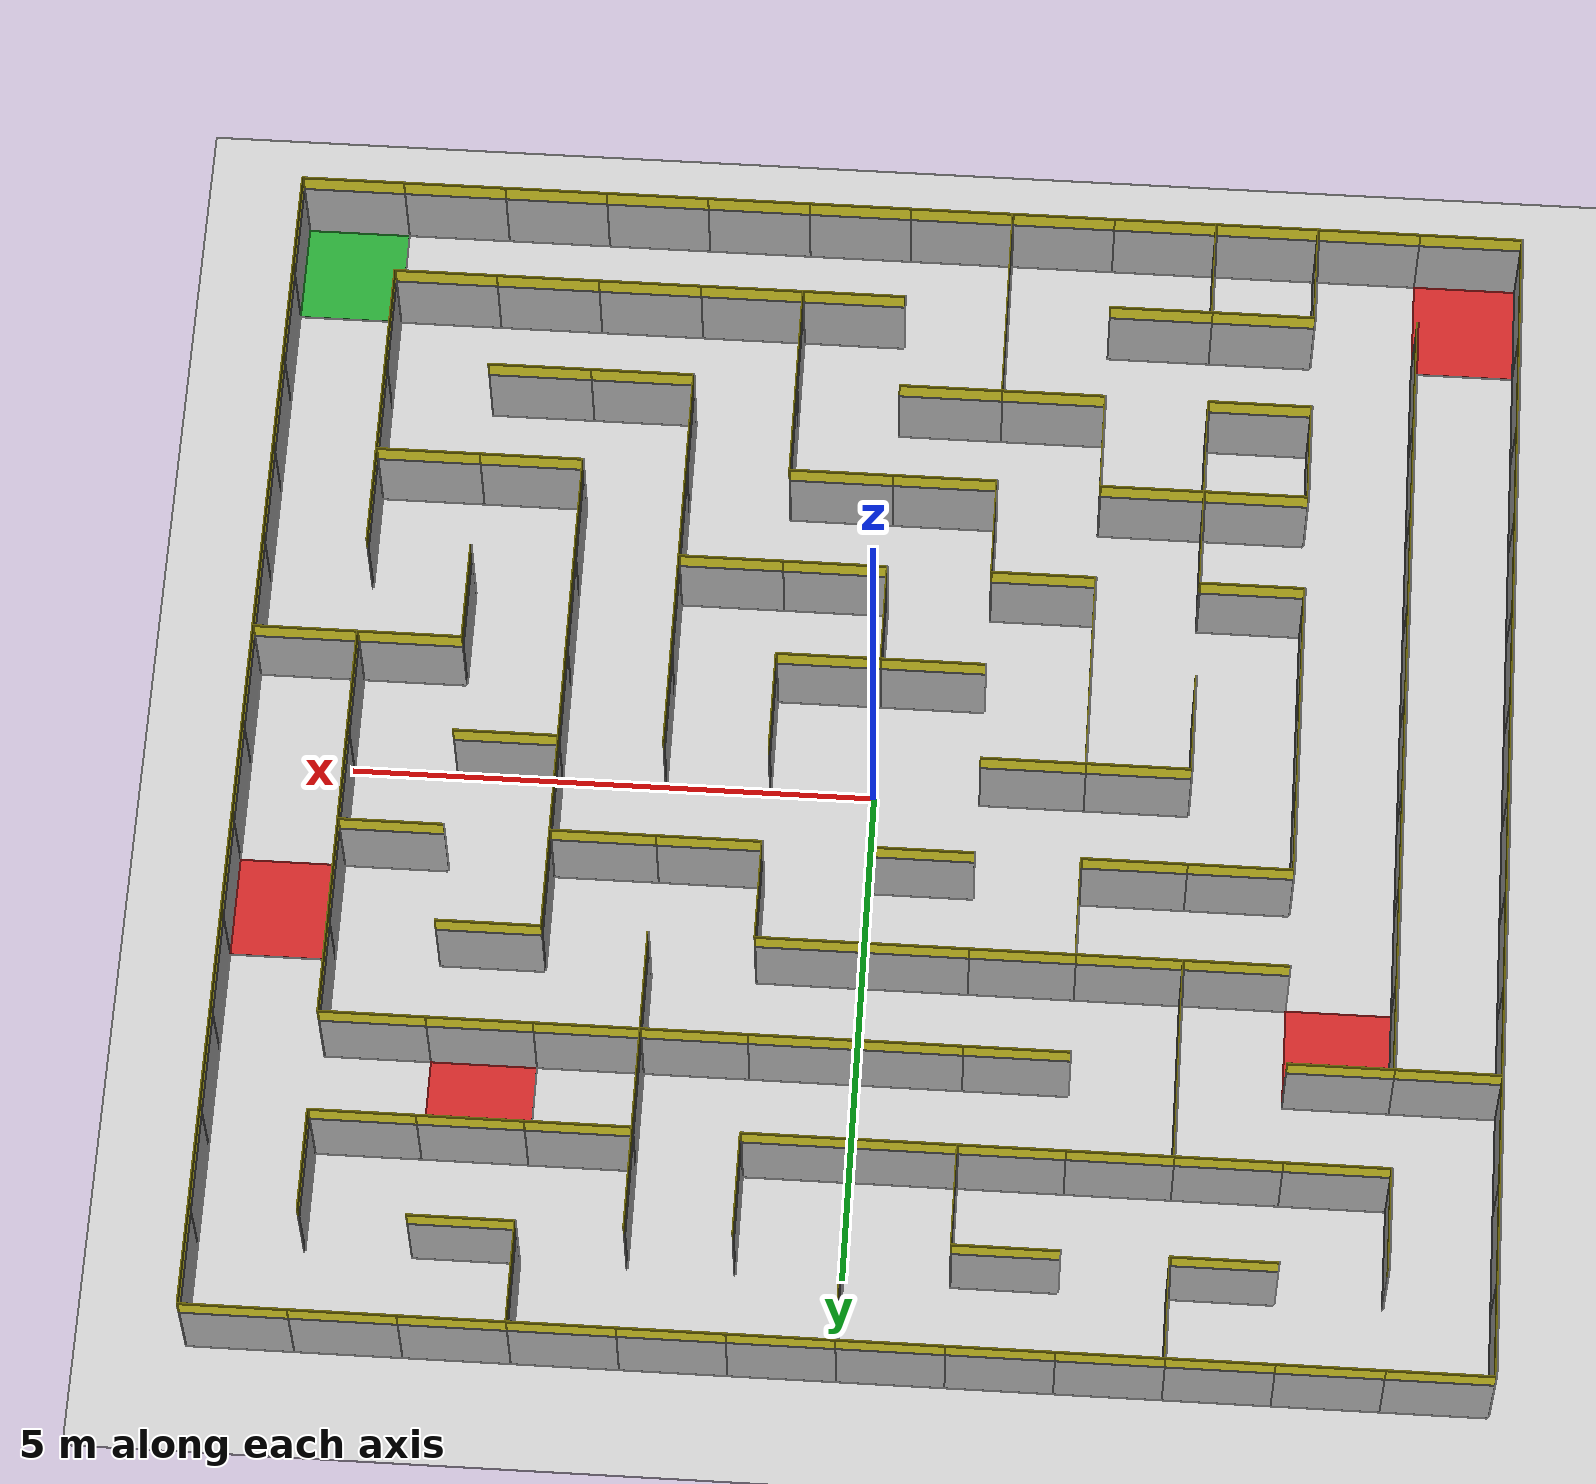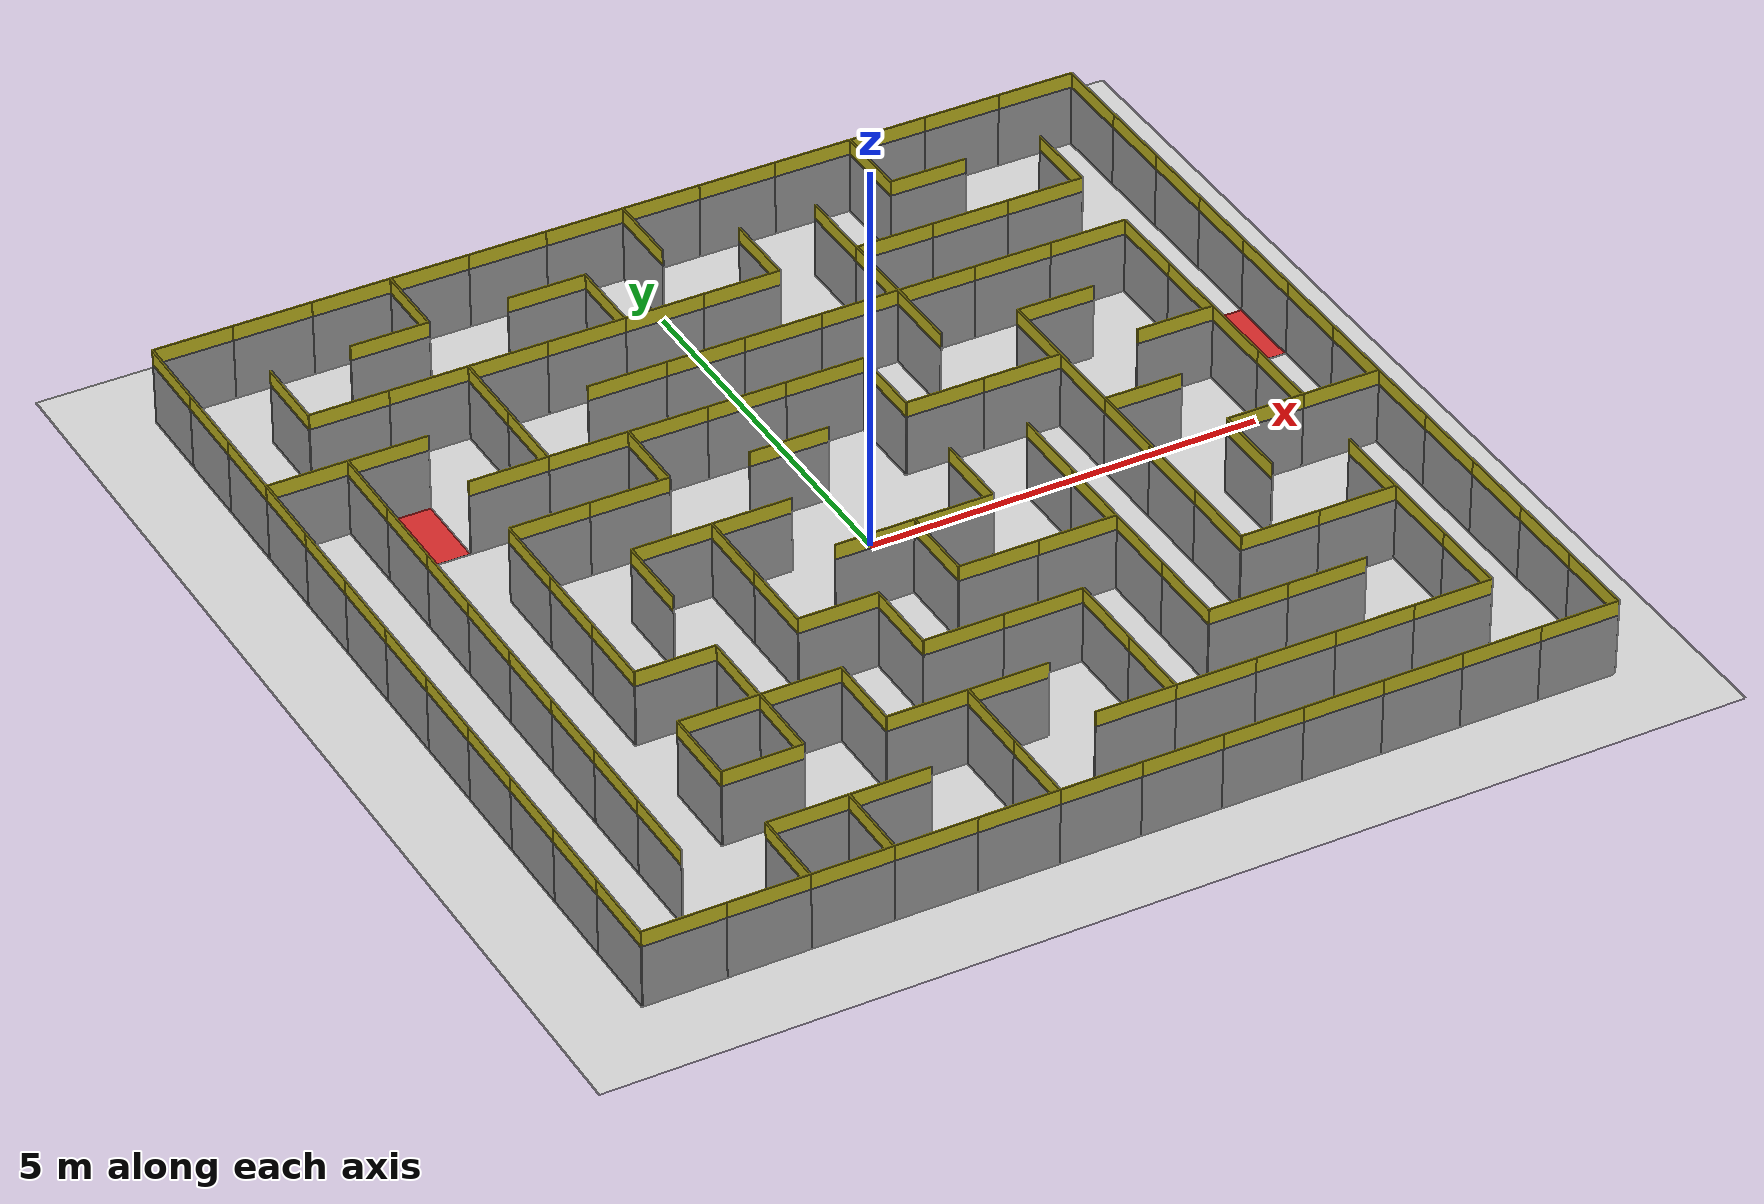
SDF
<sdf version="1.6">
 <world name="default">
  <light name="sun" type="directional">
   <cast_shadows>0</cast_shadows>
   <pose>0 0 100 0 -0 0</pose>
   <diffuse>1 1 1 1</diffuse>
   <specular>0.2 0.2 0.2 1</specular>
   <attenuation>
    <range>1000</range>
    <constant>0.9</constant>
    <linear>0.01</linear>
    <quadratic>0.001</quadratic>
   </attenuation>
   <direction>-0.5 0.1 -0.9</direction>
  </light>
  <model name="ground_plane">
   <static>1</static>
   <link name="link">
    <collision name="collision">
     <geometry><plane><normal>0 0 1</normal><size>100 100</size></plane></geometry>
     <surface>
      <contact><collide_bitmask>65535</collide_bitmask></contact>
      <friction><ode><mu>100</mu><mu2>50</mu2></ode></friction>
     </surface>
    </collision>
    <visual name="visual">
     <cast_shadows>0</cast_shadows>
     <geometry><plane><normal>0 0 1</normal><size>100 100</size></plane></geometry>
     <material>
      <script><uri>file://media/materials/scripts/gazebo.material</uri><name>Gazebo/Grey</name></script>
     </material>
    </visual>
   </link>
  </model>
  <model name="maze_base">
   <static>1</static>
   <link name="hole_1">
    <pose>5.5 1.5 0 0 -0 0</pose>
    <visual name="visual">
     <pose>0 0 0.003 0 -0 0</pose>
     <geometry><box><size>1 1 0.005</size></box></geometry>
     <material>
      <script><uri>file://media/materials/scripts/gazebo.material</uri><name>Gazebo/Red</name></script>
     </material>
    </visual>
   </link>
   <link name="hole_2">
    <pose>3.5 3.5 0 0 -0 0</pose>
    <visual name="visual">
     <pose>0 0 0.003 0 -0 0</pose>
     <geometry><box><size>1 1 0.005</size></box></geometry>
     <material>
      <script><uri>file://media/materials/scripts/gazebo.material</uri><name>Gazebo/Red</name></script>
     </material>
    </visual>
   </link>
   <link name="hole_3">
    <pose>-4.5 2.5 0 0 -0 0</pose>
    <visual name="visual">
     <pose>0 0 0.003 0 -0 0</pose>
     <geometry><box><size>1 1 0.005</size></box></geometry>
     <material>
      <script><uri>file://media/materials/scripts/gazebo.material</uri><name>Gazebo/Red</name></script>
     </material>
    </visual>
   </link>
   <link name="hole_4">
    <pose>-5.5 -5.5 0 0 -0 0</pose>
    <visual name="visual">
     <pose>0 0 0.003 0 -0 0</pose>
     <geometry><box><size>1 1 0.005</size></box></geometry>
     <material>
      <script><uri>file://media/materials/scripts/gazebo.material</uri><name>Gazebo/Red</name></script>
     </material>
    </visual>
   </link>
   <link name="destination">
    <pose>5.5 -5.5 0 0 -0 0</pose>
    <visual name="visual">
     <pose>0 0 0.003 0 -0 0</pose>
     <geometry><box><size>1 1 0.005</size></box></geometry>
     <material>
      <script><uri>file://media/materials/scripts/gazebo.material</uri><name>Gazebo/Green</name></script>
     </material>
    </visual>
   </link>
  </model>
  <plugin name="maze" filename="libmaze_plugin.so"/>
  <physics name="default_physics" default="0" type="ode">
   <max_step_size>0.01</max_step_size>
   <real_time_factor>1</real_time_factor>
   <real_time_update_rate>100</real_time_update_rate>
  </physics>
  <gravity>0 0 -9.8</gravity>
  <magnetic_field>6e-06 2.3e-05 -4.2e-05</magnetic_field>
  <atmosphere type="adiabatic"/>
  <scene><ambient>0.4 0.4 0.4 1</ambient><background>0.7 0.7 0.7 1</background><shadows>1</shadows></scene>
  <spherical_coordinates>
   <surface_model>EARTH_WGS84</surface_model>
   <latitude_deg>0</latitude_deg>
   <longitude_deg>0</longitude_deg>
   <elevation>0</elevation>
   <heading_deg>0</heading_deg>
  </spherical_coordinates>
  <model name="my_maze_1">
   <link name="__default__">
    <visual name="paint_v_0_2_S">
     <pose>-3.5 5 0.905 0 -0 0</pose>
     <geometry><box><size>1 0.012 0.2</size></box></geometry>
     <material>
      <script><name>Gazebo/Yellow</name><uri>file://media/materials/scripts/gazebo.material</uri></script>
     </material>
    </visual>
    <visual name="v_0_2_S">
     <pose>-3.5 5 0.405 0 -0 0</pose>
     <geometry><box><size>1 0.012 0.8</size></box></geometry>
    </visual>
    <collision name="p_0_2_S">
     <pose>-3.5 5 0.505 0 -0 0</pose>
     <geometry><box><size>1 0.012 1</size></box></geometry>
    </collision>
    <visual name="paint_v_0_3_W">
     <pose>-3 5.5 0.905 0 -0 1.5708</pose>
     <geometry><box><size>1 0.012 0.2</size></box></geometry>
     <material>
      <script><name>Gazebo/Yellow</name><uri>file://media/materials/scripts/gazebo.material</uri></script>
     </material>
    </visual>
    <visual name="v_0_3_W">
     <pose>-3 5.5 0.405 0 -0 1.5708</pose>
     <geometry><box><size>1 0.012 0.8</size></box></geometry>
    </visual>
    <collision name="p_0_3_W">
     <pose>-3 5.5 0.505 0 -0 1.5708</pose>
     <geometry><box><size>1 0.012 1</size></box></geometry>
    </collision>
    <visual name="paint_v_0_4_S">
     <pose>-1.5 5 0.905 0 -0 0</pose>
     <geometry><box><size>1 0.012 0.2</size></box></geometry>
     <material>
      <script><name>Gazebo/Yellow</name><uri>file://media/materials/scripts/gazebo.material</uri></script>
     </material>
    </visual>
    <visual name="v_0_4_S">
     <pose>-1.5 5 0.405 0 -0 0</pose>
     <geometry><box><size>1 0.012 0.8</size></box></geometry>
    </visual>
    <collision name="p_0_4_S">
     <pose>-1.5 5 0.505 0 -0 0</pose>
     <geometry><box><size>1 0.012 1</size></box></geometry>
    </collision>
    <visual name="paint_v_0_6_W">
     <pose>0 5.5 0.905 0 -0 1.5708</pose>
     <geometry><box><size>1 0.012 0.2</size></box></geometry>
     <material>
      <script><name>Gazebo/Yellow</name><uri>file://media/materials/scripts/gazebo.material</uri></script>
     </material>
    </visual>
    <visual name="v_0_6_W">
     <pose>0 5.5 0.405 0 -0 1.5708</pose>
     <geometry><box><size>1 0.012 0.8</size></box></geometry>
    </visual>
    <collision name="p_0_6_W">
     <pose>0 5.5 0.505 0 -0 1.5708</pose>
     <geometry><box><size>1 0.012 1</size></box></geometry>
    </collision>
    <visual name="paint_v_0_9_W">
     <pose>3 5.5 0.905 0 -0 1.5708</pose>
     <geometry><box><size>1 0.012 0.2</size></box></geometry>
     <material>
      <script><name>Gazebo/Yellow</name><uri>file://media/materials/scripts/gazebo.material</uri></script>
     </material>
    </visual>
    <visual name="v_0_9_W">
     <pose>3 5.5 0.405 0 -0 1.5708</pose>
     <geometry><box><size>1 0.012 0.8</size></box></geometry>
    </visual>
    <collision name="p_0_9_W">
     <pose>3 5.5 0.505 0 -0 1.5708</pose>
     <geometry><box><size>1 0.012 1</size></box></geometry>
    </collision>
    <visual name="paint_v_0_9_S">
     <pose>3.5 5 0.905 0 -0 0</pose>
     <geometry><box><size>1 0.012 0.2</size></box></geometry>
     <material>
      <script><name>Gazebo/Yellow</name><uri>file://media/materials/scripts/gazebo.material</uri></script>
     </material>
    </visual>
    <visual name="v_0_9_S">
     <pose>3.5 5 0.405 0 -0 0</pose>
     <geometry><box><size>1 0.012 0.8</size></box></geometry>
    </visual>
    <collision name="p_0_9_S">
     <pose>3.5 5 0.505 0 -0 0</pose>
     <geometry><box><size>1 0.012 1</size></box></geometry>
    </collision>
    <visual name="paint_v_0_0_W">
     <pose>-6 5.5 0.905 0 -0 1.5708</pose>
     <geometry><box><size>1 0.012 0.2</size></box></geometry>
     <material>
      <script><name>Gazebo/Yellow</name><uri>file://media/materials/scripts/gazebo.material</uri></script>
     </material>
    </visual>
    <visual name="v_0_0_W">
     <pose>-6 5.5 0.405 0 -0 1.5708</pose>
     <geometry><box><size>1 0.012 0.8</size></box></geometry>
    </visual>
    <collision name="p_0_0_W">
     <pose>-6 5.5 0.505 0 -0 1.5708</pose>
     <geometry><box><size>1 0.012 1</size></box></geometry>
    </collision>
    <visual name="paint_v_0_11_E">
     <pose>6 5.5 0.905 0 -0 1.5708</pose>
     <geometry><box><size>1 0.012 0.2</size></box></geometry>
     <material>
      <script><name>Gazebo/Yellow</name><uri>file://media/materials/scripts/gazebo.material</uri></script>
     </material>
    </visual>
    <visual name="v_0_11_E">
     <pose>6 5.5 0.405 0 -0 1.5708</pose>
     <geometry><box><size>1 0.012 0.8</size></box></geometry>
    </visual>
    <collision name="p_0_11_E">
     <pose>6 5.5 0.505 0 -0 1.5708</pose>
     <geometry><box><size>1 0.012 1</size></box></geometry>
    </collision>
    <visual name="paint_v_0_0_N">
     <pose>-5.5 6 0.905 0 -0 0</pose>
     <geometry><box><size>1 0.012 0.2</size></box></geometry>
     <material>
      <script><name>Gazebo/Yellow</name><uri>file://media/materials/scripts/gazebo.material</uri></script>
     </material>
    </visual>
    <visual name="v_0_0_N">
     <pose>-5.5 6 0.405 0 -0 0</pose>
     <geometry><box><size>1 0.012 0.8</size></box></geometry>
    </visual>
    <collision name="p_0_0_N">
     <pose>-5.5 6 0.505 0 -0 0</pose>
     <geometry><box><size>1 0.012 1</size></box></geometry>
    </collision>
    <visual name="paint_v_11_0_S">
     <pose>-5.5 -6 0.905 0 -0 0</pose>
     <geometry><box><size>1 0.012 0.2</size></box></geometry>
     <material>
      <script><name>Gazebo/Yellow</name><uri>file://media/materials/scripts/gazebo.material</uri></script>
     </material>
    </visual>
    <visual name="v_11_0_S">
     <pose>-5.5 -6 0.405 0 -0 0</pose>
     <geometry><box><size>1 0.012 0.8</size></box></geometry>
    </visual>
    <collision name="p_11_0_S">
     <pose>-5.5 -6 0.505 0 -0 0</pose>
     <geometry><box><size>1 0.012 1</size></box></geometry>
    </collision>
    <visual name="paint_v_1_1_W">
     <pose>-5 4.5 0.905 0 -0 1.5708</pose>
     <geometry><box><size>1 0.012 0.2</size></box></geometry>
     <material>
      <script><name>Gazebo/Yellow</name><uri>file://media/materials/scripts/gazebo.material</uri></script>
     </material>
    </visual>
    <visual name="v_1_1_W">
     <pose>-5 4.5 0.405 0 -0 1.5708</pose>
     <geometry><box><size>1 0.012 0.8</size></box></geometry>
    </visual>
    <collision name="p_1_1_W">
     <pose>-5 4.5 0.505 0 -0 1.5708</pose>
     <geometry><box><size>1 0.012 1</size></box></geometry>
    </collision>
    <visual name="paint_v_1_1_S">
     <pose>-4.5 4 0.905 0 -0 0</pose>
     <geometry><box><size>1 0.012 0.2</size></box></geometry>
     <material>
      <script><name>Gazebo/Yellow</name><uri>file://media/materials/scripts/gazebo.material</uri></script>
     </material>
    </visual>
    <visual name="v_1_1_S">
     <pose>-4.5 4 0.405 0 -0 0</pose>
     <geometry><box><size>1 0.012 0.8</size></box></geometry>
    </visual>
    <collision name="p_1_1_S">
     <pose>-4.5 4 0.505 0 -0 0</pose>
     <geometry><box><size>1 0.012 1</size></box></geometry>
    </collision>
    <visual name="paint_v_1_2_S">
     <pose>-3.5 4 0.905 0 -0 0</pose>
     <geometry><box><size>1 0.012 0.2</size></box></geometry>
     <material>
      <script><name>Gazebo/Yellow</name><uri>file://media/materials/scripts/gazebo.material</uri></script>
     </material>
    </visual>
    <visual name="v_1_2_S">
     <pose>-3.5 4 0.405 0 -0 0</pose>
     <geometry><box><size>1 0.012 0.8</size></box></geometry>
    </visual>
    <collision name="p_1_2_S">
     <pose>-3.5 4 0.505 0 -0 0</pose>
     <geometry><box><size>1 0.012 1</size></box></geometry>
    </collision>
    <visual name="paint_v_1_3_S">
     <pose>-2.5 4 0.905 0 -0 0</pose>
     <geometry><box><size>1 0.012 0.2</size></box></geometry>
     <material>
      <script><name>Gazebo/Yellow</name><uri>file://media/materials/scripts/gazebo.material</uri></script>
     </material>
    </visual>
    <visual name="v_1_3_S">
     <pose>-2.5 4 0.405 0 -0 0</pose>
     <geometry><box><size>1 0.012 0.8</size></box></geometry>
    </visual>
    <collision name="p_1_3_S">
     <pose>-2.5 4 0.505 0 -0 0</pose>
     <geometry><box><size>1 0.012 1</size></box></geometry>
    </collision>
    <visual name="paint_v_1_4_S">
     <pose>-1.5 4 0.905 0 -0 0</pose>
     <geometry><box><size>1 0.012 0.2</size></box></geometry>
     <material>
      <script><name>Gazebo/Yellow</name><uri>file://media/materials/scripts/gazebo.material</uri></script>
     </material>
    </visual>
    <visual name="v_1_4_S">
     <pose>-1.5 4 0.405 0 -0 0</pose>
     <geometry><box><size>1 0.012 0.8</size></box></geometry>
    </visual>
    <collision name="p_1_4_S">
     <pose>-1.5 4 0.505 0 -0 0</pose>
     <geometry><box><size>1 0.012 1</size></box></geometry>
    </collision>
    <visual name="paint_v_1_5_W">
     <pose>-1 4.5 0.905 0 -0 1.5708</pose>
     <geometry><box><size>1 0.012 0.2</size></box></geometry>
     <material>
      <script><name>Gazebo/Yellow</name><uri>file://media/materials/scripts/gazebo.material</uri></script>
     </material>
    </visual>
    <visual name="v_1_5_W">
     <pose>-1 4.5 0.405 0 -0 1.5708</pose>
     <geometry><box><size>1 0.012 0.8</size></box></geometry>
    </visual>
    <collision name="p_1_5_W">
     <pose>-1 4.5 0.505 0 -0 1.5708</pose>
     <geometry><box><size>1 0.012 1</size></box></geometry>
    </collision>
    <visual name="paint_v_1_5_S">
     <pose>-0.5 4 0.905 0 -0 0</pose>
     <geometry><box><size>1 0.012 0.2</size></box></geometry>
     <material>
      <script><name>Gazebo/Yellow</name><uri>file://media/materials/scripts/gazebo.material</uri></script>
     </material>
    </visual>
    <visual name="v_1_5_S">
     <pose>-0.5 4 0.405 0 -0 0</pose>
     <geometry><box><size>1 0.012 0.8</size></box></geometry>
    </visual>
    <collision name="p_1_5_S">
     <pose>-0.5 4 0.505 0 -0 0</pose>
     <geometry><box><size>1 0.012 1</size></box></geometry>
    </collision>
    <visual name="paint_v_1_6_S">
     <pose>0.5 4 0.905 0 -0 0</pose>
     <geometry><box><size>1 0.012 0.2</size></box></geometry>
     <material>
      <script><name>Gazebo/Yellow</name><uri>file://media/materials/scripts/gazebo.material</uri></script>
     </material>
    </visual>
    <visual name="v_1_6_S">
     <pose>0.5 4 0.405 0 -0 0</pose>
     <geometry><box><size>1 0.012 0.8</size></box></geometry>
    </visual>
    <collision name="p_1_6_S">
     <pose>0.5 4 0.505 0 -0 0</pose>
     <geometry><box><size>1 0.012 1</size></box></geometry>
    </collision>
    <visual name="paint_v_1_7_W">
     <pose>1 4.5 0.905 0 -0 1.5708</pose>
     <geometry><box><size>1 0.012 0.2</size></box></geometry>
     <material>
      <script><name>Gazebo/Yellow</name><uri>file://media/materials/scripts/gazebo.material</uri></script>
     </material>
    </visual>
    <visual name="v_1_7_W">
     <pose>1 4.5 0.405 0 -0 1.5708</pose>
     <geometry><box><size>1 0.012 0.8</size></box></geometry>
    </visual>
    <collision name="p_1_7_W">
     <pose>1 4.5 0.505 0 -0 1.5708</pose>
     <geometry><box><size>1 0.012 1</size></box></geometry>
    </collision>
    <visual name="paint_v_1_8_W">
     <pose>2 4.5 0.905 0 -0 1.5708</pose>
     <geometry><box><size>1 0.012 0.2</size></box></geometry>
     <material>
      <script><name>Gazebo/Yellow</name><uri>file://media/materials/scripts/gazebo.material</uri></script>
     </material>
    </visual>
    <visual name="v_1_8_W">
     <pose>2 4.5 0.405 0 -0 1.5708</pose>
     <geometry><box><size>1 0.012 0.8</size></box></geometry>
    </visual>
    <collision name="p_1_8_W">
     <pose>2 4.5 0.505 0 -0 1.5708</pose>
     <geometry><box><size>1 0.012 1</size></box></geometry>
    </collision>
    <visual name="paint_v_1_8_S">
     <pose>2.5 4 0.905 0 -0 0</pose>
     <geometry><box><size>1 0.012 0.2</size></box></geometry>
     <material>
      <script><name>Gazebo/Yellow</name><uri>file://media/materials/scripts/gazebo.material</uri></script>
     </material>
    </visual>
    <visual name="v_1_8_S">
     <pose>2.5 4 0.405 0 -0 0</pose>
     <geometry><box><size>1 0.012 0.8</size></box></geometry>
    </visual>
    <collision name="p_1_8_S">
     <pose>2.5 4 0.505 0 -0 0</pose>
     <geometry><box><size>1 0.012 1</size></box></geometry>
    </collision>
    <visual name="paint_v_1_9_S">
     <pose>3.5 4 0.905 0 -0 0</pose>
     <geometry><box><size>1 0.012 0.2</size></box></geometry>
     <material>
      <script><name>Gazebo/Yellow</name><uri>file://media/materials/scripts/gazebo.material</uri></script>
     </material>
    </visual>
    <visual name="v_1_9_S">
     <pose>3.5 4 0.405 0 -0 0</pose>
     <geometry><box><size>1 0.012 0.8</size></box></geometry>
    </visual>
    <collision name="p_1_9_S">
     <pose>3.5 4 0.505 0 -0 0</pose>
     <geometry><box><size>1 0.012 1</size></box></geometry>
    </collision>
    <visual name="paint_v_1_10_S">
     <pose>4.5 4 0.905 0 -0 0</pose>
     <geometry><box><size>1 0.012 0.2</size></box></geometry>
     <material>
      <script><name>Gazebo/Yellow</name><uri>file://media/materials/scripts/gazebo.material</uri></script>
     </material>
    </visual>
    <visual name="v_1_10_S">
     <pose>4.5 4 0.405 0 -0 0</pose>
     <geometry><box><size>1 0.012 0.8</size></box></geometry>
    </visual>
    <collision name="p_1_10_S">
     <pose>4.5 4 0.505 0 -0 0</pose>
     <geometry><box><size>1 0.012 1</size></box></geometry>
    </collision>
    <visual name="paint_v_1_11_W">
     <pose>5 4.5 0.905 0 -0 1.5708</pose>
     <geometry><box><size>1 0.012 0.2</size></box></geometry>
     <material>
      <script><name>Gazebo/Yellow</name><uri>file://media/materials/scripts/gazebo.material</uri></script>
     </material>
    </visual>
    <visual name="v_1_11_W">
     <pose>5 4.5 0.405 0 -0 1.5708</pose>
     <geometry><box><size>1 0.012 0.8</size></box></geometry>
    </visual>
    <collision name="p_1_11_W">
     <pose>5 4.5 0.505 0 -0 1.5708</pose>
     <geometry><box><size>1 0.012 1</size></box></geometry>
    </collision>
    <visual name="paint_v_1_0_W">
     <pose>-6 4.5 0.905 0 -0 1.5708</pose>
     <geometry><box><size>1 0.012 0.2</size></box></geometry>
     <material>
      <script><name>Gazebo/Yellow</name><uri>file://media/materials/scripts/gazebo.material</uri></script>
     </material>
    </visual>
    <visual name="v_1_0_W">
     <pose>-6 4.5 0.405 0 -0 1.5708</pose>
     <geometry><box><size>1 0.012 0.8</size></box></geometry>
    </visual>
    <collision name="p_1_0_W">
     <pose>-6 4.5 0.505 0 -0 1.5708</pose>
     <geometry><box><size>1 0.012 1</size></box></geometry>
    </collision>
    <visual name="paint_v_1_11_E">
     <pose>6 4.5 0.905 0 -0 1.5708</pose>
     <geometry><box><size>1 0.012 0.2</size></box></geometry>
     <material>
      <script><name>Gazebo/Yellow</name><uri>file://media/materials/scripts/gazebo.material</uri></script>
     </material>
    </visual>
    <visual name="v_1_11_E">
     <pose>6 4.5 0.405 0 -0 1.5708</pose>
     <geometry><box><size>1 0.012 0.8</size></box></geometry>
    </visual>
    <collision name="p_1_11_E">
     <pose>6 4.5 0.505 0 -0 1.5708</pose>
     <geometry><box><size>1 0.012 1</size></box></geometry>
    </collision>
    <visual name="paint_v_0_1_N">
     <pose>-4.5 6 0.905 0 -0 0</pose>
     <geometry><box><size>1 0.012 0.2</size></box></geometry>
     <material>
      <script><name>Gazebo/Yellow</name><uri>file://media/materials/scripts/gazebo.material</uri></script>
     </material>
    </visual>
    <visual name="v_0_1_N">
     <pose>-4.5 6 0.405 0 -0 0</pose>
     <geometry><box><size>1 0.012 0.8</size></box></geometry>
    </visual>
    <collision name="p_0_1_N">
     <pose>-4.5 6 0.505 0 -0 0</pose>
     <geometry><box><size>1 0.012 1</size></box></geometry>
    </collision>
    <visual name="paint_v_11_1_S">
     <pose>-4.5 -6 0.905 0 -0 0</pose>
     <geometry><box><size>1 0.012 0.2</size></box></geometry>
     <material>
      <script><name>Gazebo/Yellow</name><uri>file://media/materials/scripts/gazebo.material</uri></script>
     </material>
    </visual>
    <visual name="v_11_1_S">
     <pose>-4.5 -6 0.405 0 -0 0</pose>
     <geometry><box><size>1 0.012 0.8</size></box></geometry>
    </visual>
    <collision name="p_11_1_S">
     <pose>-4.5 -6 0.505 0 -0 0</pose>
     <geometry><box><size>1 0.012 1</size></box></geometry>
    </collision>
    <visual name="paint_v_2_0_S">
     <pose>-5.5 3 0.905 0 -0 0</pose>
     <geometry><box><size>1 0.012 0.2</size></box></geometry>
     <material>
      <script><name>Gazebo/Yellow</name><uri>file://media/materials/scripts/gazebo.material</uri></script>
     </material>
    </visual>
    <visual name="v_2_0_S">
     <pose>-5.5 3 0.405 0 -0 0</pose>
     <geometry><box><size>1 0.012 0.8</size></box></geometry>
    </visual>
    <collision name="p_2_0_S">
     <pose>-5.5 3 0.505 0 -0 0</pose>
     <geometry><box><size>1 0.012 1</size></box></geometry>
    </collision>
    <visual name="paint_v_2_1_S">
     <pose>-4.5 3 0.905 0 -0 0</pose>
     <geometry><box><size>1 0.012 0.2</size></box></geometry>
     <material>
      <script><name>Gazebo/Yellow</name><uri>file://media/materials/scripts/gazebo.material</uri></script>
     </material>
    </visual>
    <visual name="v_2_1_S">
     <pose>-4.5 3 0.405 0 -0 0</pose>
     <geometry><box><size>1 0.012 0.8</size></box></geometry>
    </visual>
    <collision name="p_2_1_S">
     <pose>-4.5 3 0.505 0 -0 0</pose>
     <geometry><box><size>1 0.012 1</size></box></geometry>
    </collision>
    <visual name="paint_v_2_3_W">
     <pose>-3 3.5 0.905 0 -0 1.5708</pose>
     <geometry><box><size>1 0.012 0.2</size></box></geometry>
     <material>
      <script><name>Gazebo/Yellow</name><uri>file://media/materials/scripts/gazebo.material</uri></script>
     </material>
    </visual>
    <visual name="v_2_3_W">
     <pose>-3 3.5 0.405 0 -0 1.5708</pose>
     <geometry><box><size>1 0.012 0.8</size></box></geometry>
    </visual>
    <collision name="p_2_3_W">
     <pose>-3 3.5 0.505 0 -0 1.5708</pose>
     <geometry><box><size>1 0.012 1</size></box></geometry>
    </collision>
    <visual name="paint_v_2_4_S">
     <pose>-1.5 3 0.905 0 -0 0</pose>
     <geometry><box><size>1 0.012 0.2</size></box></geometry>
     <material>
      <script><name>Gazebo/Yellow</name><uri>file://media/materials/scripts/gazebo.material</uri></script>
     </material>
    </visual>
    <visual name="v_2_4_S">
     <pose>-1.5 3 0.405 0 -0 0</pose>
     <geometry><box><size>1 0.012 0.8</size></box></geometry>
    </visual>
    <collision name="p_2_4_S">
     <pose>-1.5 3 0.505 0 -0 0</pose>
     <geometry><box><size>1 0.012 1</size></box></geometry>
    </collision>
    <visual name="paint_v_2_5_S">
     <pose>-0.5 3 0.905 0 -0 0</pose>
     <geometry><box><size>1 0.012 0.2</size></box></geometry>
     <material>
      <script><name>Gazebo/Yellow</name><uri>file://media/materials/scripts/gazebo.material</uri></script>
     </material>
    </visual>
    <visual name="v_2_5_S">
     <pose>-0.5 3 0.405 0 -0 0</pose>
     <geometry><box><size>1 0.012 0.8</size></box></geometry>
    </visual>
    <collision name="p_2_5_S">
     <pose>-0.5 3 0.505 0 -0 0</pose>
     <geometry><box><size>1 0.012 1</size></box></geometry>
    </collision>
    <visual name="paint_v_2_6_S">
     <pose>0.5 3 0.905 0 -0 0</pose>
     <geometry><box><size>1 0.012 0.2</size></box></geometry>
     <material>
      <script><name>Gazebo/Yellow</name><uri>file://media/materials/scripts/gazebo.material</uri></script>
     </material>
    </visual>
    <visual name="v_2_6_S">
     <pose>0.5 3 0.405 0 -0 0</pose>
     <geometry><box><size>1 0.012 0.8</size></box></geometry>
    </visual>
    <collision name="p_2_6_S">
     <pose>0.5 3 0.505 0 -0 0</pose>
     <geometry><box><size>1 0.012 1</size></box></geometry>
    </collision>
    <visual name="paint_v_2_7_S">
     <pose>1.5 3 0.905 0 -0 0</pose>
     <geometry><box><size>1 0.012 0.2</size></box></geometry>
     <material>
      <script><name>Gazebo/Yellow</name><uri>file://media/materials/scripts/gazebo.material</uri></script>
     </material>
    </visual>
    <visual name="v_2_7_S">
     <pose>1.5 3 0.405 0 -0 0</pose>
     <geometry><box><size>1 0.012 0.8</size></box></geometry>
    </visual>
    <collision name="p_2_7_S">
     <pose>1.5 3 0.505 0 -0 0</pose>
     <geometry><box><size>1 0.012 1</size></box></geometry>
    </collision>
    <visual name="paint_v_2_8_W">
     <pose>2 3.5 0.905 0 -0 1.5708</pose>
     <geometry><box><size>1 0.012 0.2</size></box></geometry>
     <material>
      <script><name>Gazebo/Yellow</name><uri>file://media/materials/scripts/gazebo.material</uri></script>
     </material>
    </visual>
    <visual name="v_2_8_W">
     <pose>2 3.5 0.405 0 -0 1.5708</pose>
     <geometry><box><size>1 0.012 0.8</size></box></geometry>
    </visual>
    <collision name="p_2_8_W">
     <pose>2 3.5 0.505 0 -0 1.5708</pose>
     <geometry><box><size>1 0.012 1</size></box></geometry>
    </collision>
    <visual name="paint_v_2_8_S">
     <pose>2.5 3 0.905 0 -0 0</pose>
     <geometry><box><size>1 0.012 0.2</size></box></geometry>
     <material>
      <script><name>Gazebo/Yellow</name><uri>file://media/materials/scripts/gazebo.material</uri></script>
     </material>
    </visual>
    <visual name="v_2_8_S">
     <pose>2.5 3 0.405 0 -0 0</pose>
     <geometry><box><size>1 0.012 0.8</size></box></geometry>
    </visual>
    <collision name="p_2_8_S">
     <pose>2.5 3 0.505 0 -0 0</pose>
     <geometry><box><size>1 0.012 1</size></box></geometry>
    </collision>
    <visual name="paint_v_2_9_S">
     <pose>3.5 3 0.905 0 -0 0</pose>
     <geometry><box><size>1 0.012 0.2</size></box></geometry>
     <material>
      <script><name>Gazebo/Yellow</name><uri>file://media/materials/scripts/gazebo.material</uri></script>
     </material>
    </visual>
    <visual name="v_2_9_S">
     <pose>3.5 3 0.405 0 -0 0</pose>
     <geometry><box><size>1 0.012 0.8</size></box></geometry>
    </visual>
    <collision name="p_2_9_S">
     <pose>3.5 3 0.505 0 -0 0</pose>
     <geometry><box><size>1 0.012 1</size></box></geometry>
    </collision>
    <visual name="paint_v_2_10_S">
     <pose>4.5 3 0.905 0 -0 0</pose>
     <geometry><box><size>1 0.012 0.2</size></box></geometry>
     <material>
      <script><name>Gazebo/Yellow</name><uri>file://media/materials/scripts/gazebo.material</uri></script>
     </material>
    </visual>
    <visual name="v_2_10_S">
     <pose>4.5 3 0.405 0 -0 0</pose>
     <geometry><box><size>1 0.012 0.8</size></box></geometry>
    </visual>
    <collision name="p_2_10_S">
     <pose>4.5 3 0.505 0 -0 0</pose>
     <geometry><box><size>1 0.012 1</size></box></geometry>
    </collision>
    <visual name="paint_v_2_0_W">
     <pose>-6 3.5 0.905 0 -0 1.5708</pose>
     <geometry><box><size>1 0.012 0.2</size></box></geometry>
     <material>
      <script><name>Gazebo/Yellow</name><uri>file://media/materials/scripts/gazebo.material</uri></script>
     </material>
    </visual>
    <visual name="v_2_0_W">
     <pose>-6 3.5 0.405 0 -0 1.5708</pose>
     <geometry><box><size>1 0.012 0.8</size></box></geometry>
    </visual>
    <collision name="p_2_0_W">
     <pose>-6 3.5 0.505 0 -0 1.5708</pose>
     <geometry><box><size>1 0.012 1</size></box></geometry>
    </collision>
    <visual name="paint_v_2_11_E">
     <pose>6 3.5 0.905 0 -0 1.5708</pose>
     <geometry><box><size>1 0.012 0.2</size></box></geometry>
     <material>
      <script><name>Gazebo/Yellow</name><uri>file://media/materials/scripts/gazebo.material</uri></script>
     </material>
    </visual>
    <visual name="v_2_11_E">
     <pose>6 3.5 0.405 0 -0 1.5708</pose>
     <geometry><box><size>1 0.012 0.8</size></box></geometry>
    </visual>
    <collision name="p_2_11_E">
     <pose>6 3.5 0.505 0 -0 1.5708</pose>
     <geometry><box><size>1 0.012 1</size></box></geometry>
    </collision>
    <visual name="paint_v_0_2_N">
     <pose>-3.5 6 0.905 0 -0 0</pose>
     <geometry><box><size>1 0.012 0.2</size></box></geometry>
     <material>
      <script><name>Gazebo/Yellow</name><uri>file://media/materials/scripts/gazebo.material</uri></script>
     </material>
    </visual>
    <visual name="v_0_2_N">
     <pose>-3.5 6 0.405 0 -0 0</pose>
     <geometry><box><size>1 0.012 0.8</size></box></geometry>
    </visual>
    <collision name="p_0_2_N">
     <pose>-3.5 6 0.505 0 -0 0</pose>
     <geometry><box><size>1 0.012 1</size></box></geometry>
    </collision>
    <visual name="paint_v_11_2_S">
     <pose>-3.5 -6 0.905 0 -0 0</pose>
     <geometry><box><size>1 0.012 0.2</size></box></geometry>
     <material>
      <script><name>Gazebo/Yellow</name><uri>file://media/materials/scripts/gazebo.material</uri></script>
     </material>
    </visual>
    <visual name="v_11_2_S">
     <pose>-3.5 -6 0.405 0 -0 0</pose>
     <geometry><box><size>1 0.012 0.8</size></box></geometry>
    </visual>
    <collision name="p_11_2_S">
     <pose>-3.5 -6 0.505 0 -0 0</pose>
     <geometry><box><size>1 0.012 1</size></box></geometry>
    </collision>
    <visual name="paint_v_3_1_W">
     <pose>-5 2.5 0.905 0 -0 1.5708</pose>
     <geometry><box><size>1 0.012 0.2</size></box></geometry>
     <material>
      <script><name>Gazebo/Yellow</name><uri>file://media/materials/scripts/gazebo.material</uri></script>
     </material>
    </visual>
    <visual name="v_3_1_W">
     <pose>-5 2.5 0.405 0 -0 1.5708</pose>
     <geometry><box><size>1 0.012 0.8</size></box></geometry>
    </visual>
    <collision name="p_3_1_W">
     <pose>-5 2.5 0.505 0 -0 1.5708</pose>
     <geometry><box><size>1 0.012 1</size></box></geometry>
    </collision>
    <visual name="paint_v_3_2_S">
     <pose>-3.5 2 0.905 0 -0 0</pose>
     <geometry><box><size>1 0.012 0.2</size></box></geometry>
     <material>
      <script><name>Gazebo/Yellow</name><uri>file://media/materials/scripts/gazebo.material</uri></script>
     </material>
    </visual>
    <visual name="v_3_2_S">
     <pose>-3.5 2 0.405 0 -0 0</pose>
     <geometry><box><size>1 0.012 0.8</size></box></geometry>
    </visual>
    <collision name="p_3_2_S">
     <pose>-3.5 2 0.505 0 -0 0</pose>
     <geometry><box><size>1 0.012 1</size></box></geometry>
    </collision>
    <visual name="paint_v_3_3_W">
     <pose>-3 2.5 0.905 0 -0 1.5708</pose>
     <geometry><box><size>1 0.012 0.2</size></box></geometry>
     <material>
      <script><name>Gazebo/Yellow</name><uri>file://media/materials/scripts/gazebo.material</uri></script>
     </material>
    </visual>
    <visual name="v_3_3_W">
     <pose>-3 2.5 0.405 0 -0 1.5708</pose>
     <geometry><box><size>1 0.012 0.8</size></box></geometry>
    </visual>
    <collision name="p_3_3_W">
     <pose>-3 2.5 0.505 0 -0 1.5708</pose>
     <geometry><box><size>1 0.012 1</size></box></geometry>
    </collision>
    <visual name="paint_v_3_3_S">
     <pose>-2.5 2 0.905 0 -0 0</pose>
     <geometry><box><size>1 0.012 0.2</size></box></geometry>
     <material>
      <script><name>Gazebo/Yellow</name><uri>file://media/materials/scripts/gazebo.material</uri></script>
     </material>
    </visual>
    <visual name="v_3_3_S">
     <pose>-2.5 2 0.405 0 -0 0</pose>
     <geometry><box><size>1 0.012 0.8</size></box></geometry>
    </visual>
    <collision name="p_3_3_S">
     <pose>-2.5 2 0.505 0 -0 0</pose>
     <geometry><box><size>1 0.012 1</size></box></geometry>
    </collision>
    <visual name="paint_v_3_4_S">
     <pose>-1.5 2 0.905 0 -0 0</pose>
     <geometry><box><size>1 0.012 0.2</size></box></geometry>
     <material>
      <script><name>Gazebo/Yellow</name><uri>file://media/materials/scripts/gazebo.material</uri></script>
     </material>
    </visual>
    <visual name="v_3_4_S">
     <pose>-1.5 2 0.405 0 -0 0</pose>
     <geometry><box><size>1 0.012 0.8</size></box></geometry>
    </visual>
    <collision name="p_3_4_S">
     <pose>-1.5 2 0.505 0 -0 0</pose>
     <geometry><box><size>1 0.012 1</size></box></geometry>
    </collision>
    <visual name="paint_v_3_5_S">
     <pose>-0.5 2 0.905 0 -0 0</pose>
     <geometry><box><size>1 0.012 0.2</size></box></geometry>
     <material>
      <script><name>Gazebo/Yellow</name><uri>file://media/materials/scripts/gazebo.material</uri></script>
     </material>
    </visual>
    <visual name="v_3_5_S">
     <pose>-0.5 2 0.405 0 -0 0</pose>
     <geometry><box><size>1 0.012 0.8</size></box></geometry>
    </visual>
    <collision name="p_3_5_S">
     <pose>-0.5 2 0.505 0 -0 0</pose>
     <geometry><box><size>1 0.012 1</size></box></geometry>
    </collision>
    <visual name="paint_v_3_6_S">
     <pose>0.5 2 0.905 0 -0 0</pose>
     <geometry><box><size>1 0.012 0.2</size></box></geometry>
     <material>
      <script><name>Gazebo/Yellow</name><uri>file://media/materials/scripts/gazebo.material</uri></script>
     </material>
    </visual>
    <visual name="v_3_6_S">
     <pose>0.5 2 0.405 0 -0 0</pose>
     <geometry><box><size>1 0.012 0.8</size></box></geometry>
    </visual>
    <collision name="p_3_6_S">
     <pose>0.5 2 0.505 0 -0 0</pose>
     <geometry><box><size>1 0.012 1</size></box></geometry>
    </collision>
    <visual name="paint_v_3_8_W">
     <pose>2 2.5 0.905 0 -0 1.5708</pose>
     <geometry><box><size>1 0.012 0.2</size></box></geometry>
     <material>
      <script><name>Gazebo/Yellow</name><uri>file://media/materials/scripts/gazebo.material</uri></script>
     </material>
    </visual>
    <visual name="v_3_8_W">
     <pose>2 2.5 0.405 0 -0 1.5708</pose>
     <geometry><box><size>1 0.012 0.8</size></box></geometry>
    </visual>
    <collision name="p_3_8_W">
     <pose>2 2.5 0.505 0 -0 1.5708</pose>
     <geometry><box><size>1 0.012 1</size></box></geometry>
    </collision>
    <visual name="paint_v_3_9_S">
     <pose>3.5 2 0.905 0 -0 0</pose>
     <geometry><box><size>1 0.012 0.2</size></box></geometry>
     <material>
      <script><name>Gazebo/Yellow</name><uri>file://media/materials/scripts/gazebo.material</uri></script>
     </material>
    </visual>
    <visual name="v_3_9_S">
     <pose>3.5 2 0.405 0 -0 0</pose>
     <geometry><box><size>1 0.012 0.8</size></box></geometry>
    </visual>
    <collision name="p_3_9_S">
     <pose>3.5 2 0.505 0 -0 0</pose>
     <geometry><box><size>1 0.012 1</size></box></geometry>
    </collision>
    <visual name="paint_v_3_11_W">
     <pose>5 2.5 0.905 0 -0 1.5708</pose>
     <geometry><box><size>1 0.012 0.2</size></box></geometry>
     <material>
      <script><name>Gazebo/Yellow</name><uri>file://media/materials/scripts/gazebo.material</uri></script>
     </material>
    </visual>
    <visual name="v_3_11_W">
     <pose>5 2.5 0.405 0 -0 1.5708</pose>
     <geometry><box><size>1 0.012 0.8</size></box></geometry>
    </visual>
    <collision name="p_3_11_W">
     <pose>5 2.5 0.505 0 -0 1.5708</pose>
     <geometry><box><size>1 0.012 1</size></box></geometry>
    </collision>
    <visual name="paint_v_3_0_W">
     <pose>-6 2.5 0.905 0 -0 1.5708</pose>
     <geometry><box><size>1 0.012 0.2</size></box></geometry>
     <material>
      <script><name>Gazebo/Yellow</name><uri>file://media/materials/scripts/gazebo.material</uri></script>
     </material>
    </visual>
    <visual name="v_3_0_W">
     <pose>-6 2.5 0.405 0 -0 1.5708</pose>
     <geometry><box><size>1 0.012 0.8</size></box></geometry>
    </visual>
    <collision name="p_3_0_W">
     <pose>-6 2.5 0.505 0 -0 1.5708</pose>
     <geometry><box><size>1 0.012 1</size></box></geometry>
    </collision>
    <visual name="paint_v_3_11_E">
     <pose>6 2.5 0.905 0 -0 1.5708</pose>
     <geometry><box><size>1 0.012 0.2</size></box></geometry>
     <material>
      <script><name>Gazebo/Yellow</name><uri>file://media/materials/scripts/gazebo.material</uri></script>
     </material>
    </visual>
    <visual name="v_3_11_E">
     <pose>6 2.5 0.405 0 -0 1.5708</pose>
     <geometry><box><size>1 0.012 0.8</size></box></geometry>
    </visual>
    <collision name="p_3_11_E">
     <pose>6 2.5 0.505 0 -0 1.5708</pose>
     <geometry><box><size>1 0.012 1</size></box></geometry>
    </collision>
    <visual name="paint_v_0_3_N">
     <pose>-2.5 6 0.905 0 -0 0</pose>
     <geometry><box><size>1 0.012 0.2</size></box></geometry>
     <material>
      <script><name>Gazebo/Yellow</name><uri>file://media/materials/scripts/gazebo.material</uri></script>
     </material>
    </visual>
    <visual name="v_0_3_N">
     <pose>-2.5 6 0.405 0 -0 0</pose>
     <geometry><box><size>1 0.012 0.8</size></box></geometry>
    </visual>
    <collision name="p_0_3_N">
     <pose>-2.5 6 0.505 0 -0 0</pose>
     <geometry><box><size>1 0.012 1</size></box></geometry>
    </collision>
    <visual name="paint_v_11_3_S">
     <pose>-2.5 -6 0.905 0 -0 0</pose>
     <geometry><box><size>1 0.012 0.2</size></box></geometry>
     <material>
      <script><name>Gazebo/Yellow</name><uri>file://media/materials/scripts/gazebo.material</uri></script>
     </material>
    </visual>
    <visual name="v_11_3_S">
     <pose>-2.5 -6 0.405 0 -0 0</pose>
     <geometry><box><size>1 0.012 0.8</size></box></geometry>
    </visual>
    <collision name="p_11_3_S">
     <pose>-2.5 -6 0.505 0 -0 0</pose>
     <geometry><box><size>1 0.012 1</size></box></geometry>
    </collision>
    <visual name="paint_v_4_1_W">
     <pose>-5 1.5 0.905 0 -0 1.5708</pose>
     <geometry><box><size>1 0.012 0.2</size></box></geometry>
     <material>
      <script><name>Gazebo/Yellow</name><uri>file://media/materials/scripts/gazebo.material</uri></script>
     </material>
    </visual>
    <visual name="v_4_1_W">
     <pose>-5 1.5 0.405 0 -0 1.5708</pose>
     <geometry><box><size>1 0.012 0.8</size></box></geometry>
    </visual>
    <collision name="p_4_1_W">
     <pose>-5 1.5 0.505 0 -0 1.5708</pose>
     <geometry><box><size>1 0.012 1</size></box></geometry>
    </collision>
    <visual name="paint_v_4_2_S">
     <pose>-3.5 1 0.905 0 -0 0</pose>
     <geometry><box><size>1 0.012 0.2</size></box></geometry>
     <material>
      <script><name>Gazebo/Yellow</name><uri>file://media/materials/scripts/gazebo.material</uri></script>
     </material>
    </visual>
    <visual name="v_4_2_S">
     <pose>-3.5 1 0.405 0 -0 0</pose>
     <geometry><box><size>1 0.012 0.8</size></box></geometry>
    </visual>
    <collision name="p_4_2_S">
     <pose>-3.5 1 0.505 0 -0 0</pose>
     <geometry><box><size>1 0.012 1</size></box></geometry>
    </collision>
    <visual name="paint_v_4_3_S">
     <pose>-2.5 1 0.905 0 -0 0</pose>
     <geometry><box><size>1 0.012 0.2</size></box></geometry>
     <material>
      <script><name>Gazebo/Yellow</name><uri>file://media/materials/scripts/gazebo.material</uri></script>
     </material>
    </visual>
    <visual name="v_4_3_S">
     <pose>-2.5 1 0.405 0 -0 0</pose>
     <geometry><box><size>1 0.012 0.8</size></box></geometry>
    </visual>
    <collision name="p_4_3_S">
     <pose>-2.5 1 0.505 0 -0 0</pose>
     <geometry><box><size>1 0.012 1</size></box></geometry>
    </collision>
    <visual name="paint_v_4_4_W">
     <pose>-2 1.5 0.905 0 -0 1.5708</pose>
     <geometry><box><size>1 0.012 0.2</size></box></geometry>
     <material>
      <script><name>Gazebo/Yellow</name><uri>file://media/materials/scripts/gazebo.material</uri></script>
     </material>
    </visual>
    <visual name="v_4_4_W">
     <pose>-2 1.5 0.405 0 -0 1.5708</pose>
     <geometry><box><size>1 0.012 0.8</size></box></geometry>
    </visual>
    <collision name="p_4_4_W">
     <pose>-2 1.5 0.505 0 -0 1.5708</pose>
     <geometry><box><size>1 0.012 1</size></box></geometry>
    </collision>
    <visual name="paint_v_4_5_S">
     <pose>-0.5 1 0.905 0 -0 0</pose>
     <geometry><box><size>1 0.012 0.2</size></box></geometry>
     <material>
      <script><name>Gazebo/Yellow</name><uri>file://media/materials/scripts/gazebo.material</uri></script>
     </material>
    </visual>
    <visual name="v_4_5_S">
     <pose>-0.5 1 0.405 0 -0 0</pose>
     <geometry><box><size>1 0.012 0.8</size></box></geometry>
    </visual>
    <collision name="p_4_5_S">
     <pose>-0.5 1 0.505 0 -0 0</pose>
     <geometry><box><size>1 0.012 1</size></box></geometry>
    </collision>
    <visual name="paint_v_4_7_W">
     <pose>1 1.5 0.905 0 -0 1.5708</pose>
     <geometry><box><size>1 0.012 0.2</size></box></geometry>
     <material>
      <script><name>Gazebo/Yellow</name><uri>file://media/materials/scripts/gazebo.material</uri></script>
     </material>
    </visual>
    <visual name="v_4_7_W">
     <pose>1 1.5 0.405 0 -0 1.5708</pose>
     <geometry><box><size>1 0.012 0.8</size></box></geometry>
    </visual>
    <collision name="p_4_7_W">
     <pose>1 1.5 0.505 0 -0 1.5708</pose>
     <geometry><box><size>1 0.012 1</size></box></geometry>
    </collision>
    <visual name="paint_v_4_7_S">
     <pose>1.5 1 0.905 0 -0 0</pose>
     <geometry><box><size>1 0.012 0.2</size></box></geometry>
     <material>
      <script><name>Gazebo/Yellow</name><uri>file://media/materials/scripts/gazebo.material</uri></script>
     </material>
    </visual>
    <visual name="v_4_7_S">
     <pose>1.5 1 0.405 0 -0 0</pose>
     <geometry><box><size>1 0.012 0.8</size></box></geometry>
    </visual>
    <collision name="p_4_7_S">
     <pose>1.5 1 0.505 0 -0 0</pose>
     <geometry><box><size>1 0.012 1</size></box></geometry>
    </collision>
    <visual name="paint_v_4_8_S">
     <pose>2.5 1 0.905 0 -0 0</pose>
     <geometry><box><size>1 0.012 0.2</size></box></geometry>
     <material>
      <script><name>Gazebo/Yellow</name><uri>file://media/materials/scripts/gazebo.material</uri></script>
     </material>
    </visual>
    <visual name="v_4_8_S">
     <pose>2.5 1 0.405 0 -0 0</pose>
     <geometry><box><size>1 0.012 0.8</size></box></geometry>
    </visual>
    <collision name="p_4_8_S">
     <pose>2.5 1 0.505 0 -0 0</pose>
     <geometry><box><size>1 0.012 1</size></box></geometry>
    </collision>
    <visual name="paint_v_4_9_W">
     <pose>3 1.5 0.905 0 -0 1.5708</pose>
     <geometry><box><size>1 0.012 0.2</size></box></geometry>
     <material>
      <script><name>Gazebo/Yellow</name><uri>file://media/materials/scripts/gazebo.material</uri></script>
     </material>
    </visual>
    <visual name="v_4_9_W">
     <pose>3 1.5 0.405 0 -0 1.5708</pose>
     <geometry><box><size>1 0.012 0.8</size></box></geometry>
    </visual>
    <collision name="p_4_9_W">
     <pose>3 1.5 0.505 0 -0 1.5708</pose>
     <geometry><box><size>1 0.012 1</size></box></geometry>
    </collision>
    <visual name="paint_v_4_10_S">
     <pose>4.5 1 0.905 0 -0 0</pose>
     <geometry><box><size>1 0.012 0.2</size></box></geometry>
     <material>
      <script><name>Gazebo/Yellow</name><uri>file://media/materials/scripts/gazebo.material</uri></script>
     </material>
    </visual>
    <visual name="v_4_10_S">
     <pose>4.5 1 0.405 0 -0 0</pose>
     <geometry><box><size>1 0.012 0.8</size></box></geometry>
    </visual>
    <collision name="p_4_10_S">
     <pose>4.5 1 0.505 0 -0 0</pose>
     <geometry><box><size>1 0.012 1</size></box></geometry>
    </collision>
    <visual name="paint_v_4_11_W">
     <pose>5 1.5 0.905 0 -0 1.5708</pose>
     <geometry><box><size>1 0.012 0.2</size></box></geometry>
     <material>
      <script><name>Gazebo/Yellow</name><uri>file://media/materials/scripts/gazebo.material</uri></script>
     </material>
    </visual>
    <visual name="v_4_11_W">
     <pose>5 1.5 0.405 0 -0 1.5708</pose>
     <geometry><box><size>1 0.012 0.8</size></box></geometry>
    </visual>
    <collision name="p_4_11_W">
     <pose>5 1.5 0.505 0 -0 1.5708</pose>
     <geometry><box><size>1 0.012 1</size></box></geometry>
    </collision>
    <visual name="paint_v_4_0_W">
     <pose>-6 1.5 0.905 0 -0 1.5708</pose>
     <geometry><box><size>1 0.012 0.2</size></box></geometry>
     <material>
      <script><name>Gazebo/Yellow</name><uri>file://media/materials/scripts/gazebo.material</uri></script>
     </material>
    </visual>
    <visual name="v_4_0_W">
     <pose>-6 1.5 0.405 0 -0 1.5708</pose>
     <geometry><box><size>1 0.012 0.8</size></box></geometry>
    </visual>
    <collision name="p_4_0_W">
     <pose>-6 1.5 0.505 0 -0 1.5708</pose>
     <geometry><box><size>1 0.012 1</size></box></geometry>
    </collision>
    <visual name="paint_v_4_11_E">
     <pose>6 1.5 0.905 0 -0 1.5708</pose>
     <geometry><box><size>1 0.012 0.2</size></box></geometry>
     <material>
      <script><name>Gazebo/Yellow</name><uri>file://media/materials/scripts/gazebo.material</uri></script>
     </material>
    </visual>
    <visual name="v_4_11_E">
     <pose>6 1.5 0.405 0 -0 1.5708</pose>
     <geometry><box><size>1 0.012 0.8</size></box></geometry>
    </visual>
    <collision name="p_4_11_E">
     <pose>6 1.5 0.505 0 -0 1.5708</pose>
     <geometry><box><size>1 0.012 1</size></box></geometry>
    </collision>
    <visual name="paint_v_0_4_N">
     <pose>-1.5 6 0.905 0 -0 0</pose>
     <geometry><box><size>1 0.012 0.2</size></box></geometry>
     <material>
      <script><name>Gazebo/Yellow</name><uri>file://media/materials/scripts/gazebo.material</uri></script>
     </material>
    </visual>
    <visual name="v_0_4_N">
     <pose>-1.5 6 0.405 0 -0 0</pose>
     <geometry><box><size>1 0.012 0.8</size></box></geometry>
    </visual>
    <collision name="p_0_4_N">
     <pose>-1.5 6 0.505 0 -0 0</pose>
     <geometry><box><size>1 0.012 1</size></box></geometry>
    </collision>
    <visual name="paint_v_11_4_S">
     <pose>-1.5 -6 0.905 0 -0 0</pose>
     <geometry><box><size>1 0.012 0.2</size></box></geometry>
     <material>
      <script><name>Gazebo/Yellow</name><uri>file://media/materials/scripts/gazebo.material</uri></script>
     </material>
    </visual>
    <visual name="v_11_4_S">
     <pose>-1.5 -6 0.405 0 -0 0</pose>
     <geometry><box><size>1 0.012 0.8</size></box></geometry>
    </visual>
    <collision name="p_11_4_S">
     <pose>-1.5 -6 0.505 0 -0 0</pose>
     <geometry><box><size>1 0.012 1</size></box></geometry>
    </collision>
    <visual name="paint_v_5_1_W">
     <pose>-5 0.5 0.905 0 -0 1.5708</pose>
     <geometry><box><size>1 0.012 0.2</size></box></geometry>
     <material>
      <script><name>Gazebo/Yellow</name><uri>file://media/materials/scripts/gazebo.material</uri></script>
     </material>
    </visual>
    <visual name="v_5_1_W">
     <pose>-5 0.5 0.405 0 -0 1.5708</pose>
     <geometry><box><size>1 0.012 0.8</size></box></geometry>
    </visual>
    <collision name="p_5_1_W">
     <pose>-5 0.5 0.505 0 -0 1.5708</pose>
     <geometry><box><size>1 0.012 1</size></box></geometry>
    </collision>
    <visual name="paint_v_5_2_W">
     <pose>-4 0.5 0.905 0 -0 1.5708</pose>
     <geometry><box><size>1 0.012 0.2</size></box></geometry>
     <material>
      <script><name>Gazebo/Yellow</name><uri>file://media/materials/scripts/gazebo.material</uri></script>
     </material>
    </visual>
    <visual name="v_5_2_W">
     <pose>-4 0.5 0.405 0 -0 1.5708</pose>
     <geometry><box><size>1 0.012 0.8</size></box></geometry>
    </visual>
    <collision name="p_5_2_W">
     <pose>-4 0.5 0.505 0 -0 1.5708</pose>
     <geometry><box><size>1 0.012 1</size></box></geometry>
    </collision>
    <visual name="paint_v_5_3_S">
     <pose>-2.5 0 0.905 0 -0 0</pose>
     <geometry><box><size>1 0.012 0.2</size></box></geometry>
     <material>
      <script><name>Gazebo/Yellow</name><uri>file://media/materials/scripts/gazebo.material</uri></script>
     </material>
    </visual>
    <visual name="v_5_3_S">
     <pose>-2.5 0 0.405 0 -0 0</pose>
     <geometry><box><size>1 0.012 0.8</size></box></geometry>
    </visual>
    <collision name="p_5_3_S">
     <pose>-2.5 0 0.505 0 -0 0</pose>
     <geometry><box><size>1 0.012 1</size></box></geometry>
    </collision>
    <visual name="paint_v_5_4_S">
     <pose>-1.5 0 0.905 0 -0 0</pose>
     <geometry><box><size>1 0.012 0.2</size></box></geometry>
     <material>
      <script><name>Gazebo/Yellow</name><uri>file://media/materials/scripts/gazebo.material</uri></script>
     </material>
    </visual>
    <visual name="v_5_4_S">
     <pose>-1.5 0 0.405 0 -0 0</pose>
     <geometry><box><size>1 0.012 0.8</size></box></geometry>
    </visual>
    <collision name="p_5_4_S">
     <pose>-1.5 0 0.505 0 -0 0</pose>
     <geometry><box><size>1 0.012 1</size></box></geometry>
    </collision>
    <visual name="paint_v_5_9_W">
     <pose>3 0.5 0.905 0 -0 1.5708</pose>
     <geometry><box><size>1 0.012 0.2</size></box></geometry>
     <material>
      <script><name>Gazebo/Yellow</name><uri>file://media/materials/scripts/gazebo.material</uri></script>
     </material>
    </visual>
    <visual name="v_5_9_W">
     <pose>3 0.5 0.405 0 -0 1.5708</pose>
     <geometry><box><size>1 0.012 0.8</size></box></geometry>
    </visual>
    <collision name="p_5_9_W">
     <pose>3 0.5 0.505 0 -0 1.5708</pose>
     <geometry><box><size>1 0.012 1</size></box></geometry>
    </collision>
    <visual name="paint_v_5_9_S">
     <pose>3.5 0 0.905 0 -0 0</pose>
     <geometry><box><size>1 0.012 0.2</size></box></geometry>
     <material>
      <script><name>Gazebo/Yellow</name><uri>file://media/materials/scripts/gazebo.material</uri></script>
     </material>
    </visual>
    <visual name="v_5_9_S">
     <pose>3.5 0 0.405 0 -0 0</pose>
     <geometry><box><size>1 0.012 0.8</size></box></geometry>
    </visual>
    <collision name="p_5_9_S">
     <pose>3.5 0 0.505 0 -0 0</pose>
     <geometry><box><size>1 0.012 1</size></box></geometry>
    </collision>
    <visual name="paint_v_5_11_W">
     <pose>5 0.5 0.905 0 -0 1.5708</pose>
     <geometry><box><size>1 0.012 0.2</size></box></geometry>
     <material>
      <script><name>Gazebo/Yellow</name><uri>file://media/materials/scripts/gazebo.material</uri></script>
     </material>
    </visual>
    <visual name="v_5_11_W">
     <pose>5 0.5 0.405 0 -0 1.5708</pose>
     <geometry><box><size>1 0.012 0.8</size></box></geometry>
    </visual>
    <collision name="p_5_11_W">
     <pose>5 0.5 0.505 0 -0 1.5708</pose>
     <geometry><box><size>1 0.012 1</size></box></geometry>
    </collision>
    <visual name="paint_v_5_0_W">
     <pose>-6 0.5 0.905 0 -0 1.5708</pose>
     <geometry><box><size>1 0.012 0.2</size></box></geometry>
     <material>
      <script><name>Gazebo/Yellow</name><uri>file://media/materials/scripts/gazebo.material</uri></script>
     </material>
    </visual>
    <visual name="v_5_0_W">
     <pose>-6 0.5 0.405 0 -0 1.5708</pose>
     <geometry><box><size>1 0.012 0.8</size></box></geometry>
    </visual>
    <collision name="p_5_0_W">
     <pose>-6 0.5 0.505 0 -0 1.5708</pose>
     <geometry><box><size>1 0.012 1</size></box></geometry>
    </collision>
    <visual name="paint_v_5_11_E">
     <pose>6 0.5 0.905 0 -0 1.5708</pose>
     <geometry><box><size>1 0.012 0.2</size></box></geometry>
     <material>
      <script><name>Gazebo/Yellow</name><uri>file://media/materials/scripts/gazebo.material</uri></script>
     </material>
    </visual>
    <visual name="v_5_11_E">
     <pose>6 0.5 0.405 0 -0 1.5708</pose>
     <geometry><box><size>1 0.012 0.8</size></box></geometry>
    </visual>
    <collision name="p_5_11_E">
     <pose>6 0.5 0.505 0 -0 1.5708</pose>
     <geometry><box><size>1 0.012 1</size></box></geometry>
    </collision>
    <visual name="paint_v_0_5_N">
     <pose>-0.5 6 0.905 0 -0 0</pose>
     <geometry><box><size>1 0.012 0.2</size></box></geometry>
     <material>
      <script><name>Gazebo/Yellow</name><uri>file://media/materials/scripts/gazebo.material</uri></script>
     </material>
    </visual>
    <visual name="v_0_5_N">
     <pose>-0.5 6 0.405 0 -0 0</pose>
     <geometry><box><size>1 0.012 0.8</size></box></geometry>
    </visual>
    <collision name="p_0_5_N">
     <pose>-0.5 6 0.505 0 -0 0</pose>
     <geometry><box><size>1 0.012 1</size></box></geometry>
    </collision>
    <visual name="paint_v_11_5_S">
     <pose>-0.5 -6 0.905 0 -0 0</pose>
     <geometry><box><size>1 0.012 0.2</size></box></geometry>
     <material>
      <script><name>Gazebo/Yellow</name><uri>file://media/materials/scripts/gazebo.material</uri></script>
     </material>
    </visual>
    <visual name="v_11_5_S">
     <pose>-0.5 -6 0.405 0 -0 0</pose>
     <geometry><box><size>1 0.012 0.8</size></box></geometry>
    </visual>
    <collision name="p_11_5_S">
     <pose>-0.5 -6 0.505 0 -0 0</pose>
     <geometry><box><size>1 0.012 1</size></box></geometry>
    </collision>
    <visual name="paint_v_6_1_W">
     <pose>-5 -0.5 0.905 0 -0 1.5708</pose>
     <geometry><box><size>1 0.012 0.2</size></box></geometry>
     <material>
      <script><name>Gazebo/Yellow</name><uri>file://media/materials/scripts/gazebo.material</uri></script>
     </material>
    </visual>
    <visual name="v_6_1_W">
     <pose>-5 -0.5 0.405 0 -0 1.5708</pose>
     <geometry><box><size>1 0.012 0.8</size></box></geometry>
    </visual>
    <collision name="p_6_1_W">
     <pose>-5 -0.5 0.505 0 -0 1.5708</pose>
     <geometry><box><size>1 0.012 1</size></box></geometry>
    </collision>
    <visual name="paint_v_6_2_W">
     <pose>-4 -0.5 0.905 0 -0 1.5708</pose>
     <geometry><box><size>1 0.012 0.2</size></box></geometry>
     <material>
      <script><name>Gazebo/Yellow</name><uri>file://media/materials/scripts/gazebo.material</uri></script>
     </material>
    </visual>
    <visual name="v_6_2_W">
     <pose>-4 -0.5 0.405 0 -0 1.5708</pose>
     <geometry><box><size>1 0.012 0.8</size></box></geometry>
    </visual>
    <collision name="p_6_2_W">
     <pose>-4 -0.5 0.505 0 -0 1.5708</pose>
     <geometry><box><size>1 0.012 1</size></box></geometry>
    </collision>
    <visual name="paint_v_6_3_W">
     <pose>-3 -0.5 0.905 0 -0 1.5708</pose>
     <geometry><box><size>1 0.012 0.2</size></box></geometry>
     <material>
      <script><name>Gazebo/Yellow</name><uri>file://media/materials/scripts/gazebo.material</uri></script>
     </material>
    </visual>
    <visual name="v_6_3_W">
     <pose>-3 -0.5 0.405 0 -0 1.5708</pose>
     <geometry><box><size>1 0.012 0.8</size></box></geometry>
    </visual>
    <collision name="p_6_3_W">
     <pose>-3 -0.5 0.505 0 -0 1.5708</pose>
     <geometry><box><size>1 0.012 1</size></box></geometry>
    </collision>
    <visual name="paint_v_6_4_W">
     <pose>-2 -0.5 0.905 0 -0 1.5708</pose>
     <geometry><box><size>1 0.012 0.2</size></box></geometry>
     <material>
      <script><name>Gazebo/Yellow</name><uri>file://media/materials/scripts/gazebo.material</uri></script>
     </material>
    </visual>
    <visual name="v_6_4_W">
     <pose>-2 -0.5 0.405 0 -0 1.5708</pose>
     <geometry><box><size>1 0.012 0.8</size></box></geometry>
    </visual>
    <collision name="p_6_4_W">
     <pose>-2 -0.5 0.505 0 -0 1.5708</pose>
     <geometry><box><size>1 0.012 1</size></box></geometry>
    </collision>
    <visual name="paint_v_6_5_S">
     <pose>-0.5 -1 0.905 0 -0 0</pose>
     <geometry><box><size>1 0.012 0.2</size></box></geometry>
     <material>
      <script><name>Gazebo/Yellow</name><uri>file://media/materials/scripts/gazebo.material</uri></script>
     </material>
    </visual>
    <visual name="v_6_5_S">
     <pose>-0.5 -1 0.405 0 -0 0</pose>
     <geometry><box><size>1 0.012 0.8</size></box></geometry>
    </visual>
    <collision name="p_6_5_S">
     <pose>-0.5 -1 0.505 0 -0 0</pose>
     <geometry><box><size>1 0.012 1</size></box></geometry>
    </collision>
    <visual name="paint_v_6_6_S">
     <pose>0.5 -1 0.905 0 -0 0</pose>
     <geometry><box><size>1 0.012 0.2</size></box></geometry>
     <material>
      <script><name>Gazebo/Yellow</name><uri>file://media/materials/scripts/gazebo.material</uri></script>
     </material>
    </visual>
    <visual name="v_6_6_S">
     <pose>0.5 -1 0.405 0 -0 0</pose>
     <geometry><box><size>1 0.012 0.8</size></box></geometry>
    </visual>
    <collision name="p_6_6_S">
     <pose>0.5 -1 0.505 0 -0 0</pose>
     <geometry><box><size>1 0.012 1</size></box></geometry>
    </collision>
    <visual name="paint_v_6_7_W">
     <pose>1 -0.5 0.905 0 -0 1.5708</pose>
     <geometry><box><size>1 0.012 0.2</size></box></geometry>
     <material>
      <script><name>Gazebo/Yellow</name><uri>file://media/materials/scripts/gazebo.material</uri></script>
     </material>
    </visual>
    <visual name="v_6_7_W">
     <pose>1 -0.5 0.405 0 -0 1.5708</pose>
     <geometry><box><size>1 0.012 0.8</size></box></geometry>
    </visual>
    <collision name="p_6_7_W">
     <pose>1 -0.5 0.505 0 -0 1.5708</pose>
     <geometry><box><size>1 0.012 1</size></box></geometry>
    </collision>
    <visual name="paint_v_6_8_W">
     <pose>2 -0.5 0.905 0 -0 1.5708</pose>
     <geometry><box><size>1 0.012 0.2</size></box></geometry>
     <material>
      <script><name>Gazebo/Yellow</name><uri>file://media/materials/scripts/gazebo.material</uri></script>
     </material>
    </visual>
    <visual name="v_6_8_W">
     <pose>2 -0.5 0.405 0 -0 1.5708</pose>
     <geometry><box><size>1 0.012 0.8</size></box></geometry>
    </visual>
    <collision name="p_6_8_W">
     <pose>2 -0.5 0.505 0 -0 1.5708</pose>
     <geometry><box><size>1 0.012 1</size></box></geometry>
    </collision>
    <visual name="paint_v_6_9_W">
     <pose>3 -0.5 0.905 0 -0 1.5708</pose>
     <geometry><box><size>1 0.012 0.2</size></box></geometry>
     <material>
      <script><name>Gazebo/Yellow</name><uri>file://media/materials/scripts/gazebo.material</uri></script>
     </material>
    </visual>
    <visual name="v_6_9_W">
     <pose>3 -0.5 0.405 0 -0 1.5708</pose>
     <geometry><box><size>1 0.012 0.8</size></box></geometry>
    </visual>
    <collision name="p_6_9_W">
     <pose>3 -0.5 0.505 0 -0 1.5708</pose>
     <geometry><box><size>1 0.012 1</size></box></geometry>
    </collision>
    <visual name="paint_v_6_10_S">
     <pose>4.5 -1 0.905 0 -0 0</pose>
     <geometry><box><size>1 0.012 0.2</size></box></geometry>
     <material>
      <script><name>Gazebo/Yellow</name><uri>file://media/materials/scripts/gazebo.material</uri></script>
     </material>
    </visual>
    <visual name="v_6_10_S">
     <pose>4.5 -1 0.405 0 -0 0</pose>
     <geometry><box><size>1 0.012 0.8</size></box></geometry>
    </visual>
    <collision name="p_6_10_S">
     <pose>4.5 -1 0.505 0 -0 0</pose>
     <geometry><box><size>1 0.012 1</size></box></geometry>
    </collision>
    <visual name="paint_v_6_11_W">
     <pose>5 -0.5 0.905 0 -0 1.5708</pose>
     <geometry><box><size>1 0.012 0.2</size></box></geometry>
     <material>
      <script><name>Gazebo/Yellow</name><uri>file://media/materials/scripts/gazebo.material</uri></script>
     </material>
    </visual>
    <visual name="v_6_11_W">
     <pose>5 -0.5 0.405 0 -0 1.5708</pose>
     <geometry><box><size>1 0.012 0.8</size></box></geometry>
    </visual>
    <collision name="p_6_11_W">
     <pose>5 -0.5 0.505 0 -0 1.5708</pose>
     <geometry><box><size>1 0.012 1</size></box></geometry>
    </collision>
    <visual name="paint_v_6_11_S">
     <pose>5.5 -1 0.905 0 -0 0</pose>
     <geometry><box><size>1 0.012 0.2</size></box></geometry>
     <material>
      <script><name>Gazebo/Yellow</name><uri>file://media/materials/scripts/gazebo.material</uri></script>
     </material>
    </visual>
    <visual name="v_6_11_S">
     <pose>5.5 -1 0.405 0 -0 0</pose>
     <geometry><box><size>1 0.012 0.8</size></box></geometry>
    </visual>
    <collision name="p_6_11_S">
     <pose>5.5 -1 0.505 0 -0 0</pose>
     <geometry><box><size>1 0.012 1</size></box></geometry>
    </collision>
    <visual name="paint_v_6_0_W">
     <pose>-6 -0.5 0.905 0 -0 1.5708</pose>
     <geometry><box><size>1 0.012 0.2</size></box></geometry>
     <material>
      <script><name>Gazebo/Yellow</name><uri>file://media/materials/scripts/gazebo.material</uri></script>
     </material>
    </visual>
    <visual name="v_6_0_W">
     <pose>-6 -0.5 0.405 0 -0 1.5708</pose>
     <geometry><box><size>1 0.012 0.8</size></box></geometry>
    </visual>
    <collision name="p_6_0_W">
     <pose>-6 -0.5 0.505 0 -0 1.5708</pose>
     <geometry><box><size>1 0.012 1</size></box></geometry>
    </collision>
    <visual name="paint_v_6_11_E">
     <pose>6 -0.5 0.905 0 -0 1.5708</pose>
     <geometry><box><size>1 0.012 0.2</size></box></geometry>
     <material>
      <script><name>Gazebo/Yellow</name><uri>file://media/materials/scripts/gazebo.material</uri></script>
     </material>
    </visual>
    <visual name="v_6_11_E">
     <pose>6 -0.5 0.405 0 -0 1.5708</pose>
     <geometry><box><size>1 0.012 0.8</size></box></geometry>
    </visual>
    <collision name="p_6_11_E">
     <pose>6 -0.5 0.505 0 -0 1.5708</pose>
     <geometry><box><size>1 0.012 1</size></box></geometry>
    </collision>
    <visual name="paint_v_0_6_N">
     <pose>0.5 6 0.905 0 -0 0</pose>
     <geometry><box><size>1 0.012 0.2</size></box></geometry>
     <material>
      <script><name>Gazebo/Yellow</name><uri>file://media/materials/scripts/gazebo.material</uri></script>
     </material>
    </visual>
    <visual name="v_0_6_N">
     <pose>0.5 6 0.405 0 -0 0</pose>
     <geometry><box><size>1 0.012 0.8</size></box></geometry>
    </visual>
    <collision name="p_0_6_N">
     <pose>0.5 6 0.505 0 -0 0</pose>
     <geometry><box><size>1 0.012 1</size></box></geometry>
    </collision>
    <visual name="paint_v_11_6_S">
     <pose>0.5 -6 0.905 0 -0 0</pose>
     <geometry><box><size>1 0.012 0.2</size></box></geometry>
     <material>
      <script><name>Gazebo/Yellow</name><uri>file://media/materials/scripts/gazebo.material</uri></script>
     </material>
    </visual>
    <visual name="v_11_6_S">
     <pose>0.5 -6 0.405 0 -0 0</pose>
     <geometry><box><size>1 0.012 0.8</size></box></geometry>
    </visual>
    <collision name="p_11_6_S">
     <pose>0.5 -6 0.505 0 -0 0</pose>
     <geometry><box><size>1 0.012 1</size></box></geometry>
    </collision>
    <visual name="paint_v_7_1_W">
     <pose>-5 -1.5 0.905 0 -0 1.5708</pose>
     <geometry><box><size>1 0.012 0.2</size></box></geometry>
     <material>
      <script><name>Gazebo/Yellow</name><uri>file://media/materials/scripts/gazebo.material</uri></script>
     </material>
    </visual>
    <visual name="v_7_1_W">
     <pose>-5 -1.5 0.405 0 -0 1.5708</pose>
     <geometry><box><size>1 0.012 0.8</size></box></geometry>
    </visual>
    <collision name="p_7_1_W">
     <pose>-5 -1.5 0.505 0 -0 1.5708</pose>
     <geometry><box><size>1 0.012 1</size></box></geometry>
    </collision>
    <visual name="paint_v_7_2_W">
     <pose>-4 -1.5 0.905 0 -0 1.5708</pose>
     <geometry><box><size>1 0.012 0.2</size></box></geometry>
     <material>
      <script><name>Gazebo/Yellow</name><uri>file://media/materials/scripts/gazebo.material</uri></script>
     </material>
    </visual>
    <visual name="v_7_2_W">
     <pose>-4 -1.5 0.405 0 -0 1.5708</pose>
     <geometry><box><size>1 0.012 0.8</size></box></geometry>
    </visual>
    <collision name="p_7_2_W">
     <pose>-4 -1.5 0.505 0 -0 1.5708</pose>
     <geometry><box><size>1 0.012 1</size></box></geometry>
    </collision>
    <visual name="paint_v_7_2_S">
     <pose>-3.5 -2 0.905 0 -0 0</pose>
     <geometry><box><size>1 0.012 0.2</size></box></geometry>
     <material>
      <script><name>Gazebo/Yellow</name><uri>file://media/materials/scripts/gazebo.material</uri></script>
     </material>
    </visual>
    <visual name="v_7_2_S">
     <pose>-3.5 -2 0.405 0 -0 0</pose>
     <geometry><box><size>1 0.012 0.8</size></box></geometry>
    </visual>
    <collision name="p_7_2_S">
     <pose>-3.5 -2 0.505 0 -0 0</pose>
     <geometry><box><size>1 0.012 1</size></box></geometry>
    </collision>
    <visual name="paint_v_7_4_W">
     <pose>-2 -1.5 0.905 0 -0 1.5708</pose>
     <geometry><box><size>1 0.012 0.2</size></box></geometry>
     <material>
      <script><name>Gazebo/Yellow</name><uri>file://media/materials/scripts/gazebo.material</uri></script>
     </material>
    </visual>
    <visual name="v_7_4_W">
     <pose>-2 -1.5 0.405 0 -0 1.5708</pose>
     <geometry><box><size>1 0.012 0.8</size></box></geometry>
    </visual>
    <collision name="p_7_4_W">
     <pose>-2 -1.5 0.505 0 -0 1.5708</pose>
     <geometry><box><size>1 0.012 1</size></box></geometry>
    </collision>
    <visual name="paint_v_7_4_S">
     <pose>-1.5 -2 0.905 0 -0 0</pose>
     <geometry><box><size>1 0.012 0.2</size></box></geometry>
     <material>
      <script><name>Gazebo/Yellow</name><uri>file://media/materials/scripts/gazebo.material</uri></script>
     </material>
    </visual>
    <visual name="v_7_4_S">
     <pose>-1.5 -2 0.405 0 -0 0</pose>
     <geometry><box><size>1 0.012 0.8</size></box></geometry>
    </visual>
    <collision name="p_7_4_S">
     <pose>-1.5 -2 0.505 0 -0 0</pose>
     <geometry><box><size>1 0.012 1</size></box></geometry>
    </collision>
    <visual name="paint_v_7_6_W">
     <pose>0 -1.5 0.905 0 -0 1.5708</pose>
     <geometry><box><size>1 0.012 0.2</size></box></geometry>
     <material>
      <script><name>Gazebo/Yellow</name><uri>file://media/materials/scripts/gazebo.material</uri></script>
     </material>
    </visual>
    <visual name="v_7_6_W">
     <pose>0 -1.5 0.405 0 -0 1.5708</pose>
     <geometry><box><size>1 0.012 0.8</size></box></geometry>
    </visual>
    <collision name="p_7_6_W">
     <pose>0 -1.5 0.505 0 -0 1.5708</pose>
     <geometry><box><size>1 0.012 1</size></box></geometry>
    </collision>
    <visual name="paint_v_7_6_S">
     <pose>0.5 -2 0.905 0 -0 0</pose>
     <geometry><box><size>1 0.012 0.2</size></box></geometry>
     <material>
      <script><name>Gazebo/Yellow</name><uri>file://media/materials/scripts/gazebo.material</uri></script>
     </material>
    </visual>
    <visual name="v_7_6_S">
     <pose>0.5 -2 0.405 0 -0 0</pose>
     <geometry><box><size>1 0.012 0.8</size></box></geometry>
    </visual>
    <collision name="p_7_6_S">
     <pose>0.5 -2 0.505 0 -0 0</pose>
     <geometry><box><size>1 0.012 1</size></box></geometry>
    </collision>
    <visual name="paint_v_7_7_S">
     <pose>1.5 -2 0.905 0 -0 0</pose>
     <geometry><box><size>1 0.012 0.2</size></box></geometry>
     <material>
      <script><name>Gazebo/Yellow</name><uri>file://media/materials/scripts/gazebo.material</uri></script>
     </material>
    </visual>
    <visual name="v_7_7_S">
     <pose>1.5 -2 0.405 0 -0 0</pose>
     <geometry><box><size>1 0.012 0.8</size></box></geometry>
    </visual>
    <collision name="p_7_7_S">
     <pose>1.5 -2 0.505 0 -0 0</pose>
     <geometry><box><size>1 0.012 1</size></box></geometry>
    </collision>
    <visual name="paint_v_7_8_W">
     <pose>2 -1.5 0.905 0 -0 1.5708</pose>
     <geometry><box><size>1 0.012 0.2</size></box></geometry>
     <material>
      <script><name>Gazebo/Yellow</name><uri>file://media/materials/scripts/gazebo.material</uri></script>
     </material>
    </visual>
    <visual name="v_7_8_W">
     <pose>2 -1.5 0.405 0 -0 1.5708</pose>
     <geometry><box><size>1 0.012 0.8</size></box></geometry>
    </visual>
    <collision name="p_7_8_W">
     <pose>2 -1.5 0.505 0 -0 1.5708</pose>
     <geometry><box><size>1 0.012 1</size></box></geometry>
    </collision>
    <visual name="paint_v_7_9_W">
     <pose>3 -1.5 0.905 0 -0 1.5708</pose>
     <geometry><box><size>1 0.012 0.2</size></box></geometry>
     <material>
      <script><name>Gazebo/Yellow</name><uri>file://media/materials/scripts/gazebo.material</uri></script>
     </material>
    </visual>
    <visual name="v_7_9_W">
     <pose>3 -1.5 0.405 0 -0 1.5708</pose>
     <geometry><box><size>1 0.012 0.8</size></box></geometry>
    </visual>
    <collision name="p_7_9_W">
     <pose>3 -1.5 0.505 0 -0 1.5708</pose>
     <geometry><box><size>1 0.012 1</size></box></geometry>
    </collision>
    <visual name="paint_v_7_10_W">
     <pose>4 -1.5 0.905 0 -0 1.5708</pose>
     <geometry><box><size>1 0.012 0.2</size></box></geometry>
     <material>
      <script><name>Gazebo/Yellow</name><uri>file://media/materials/scripts/gazebo.material</uri></script>
     </material>
    </visual>
    <visual name="v_7_10_W">
     <pose>4 -1.5 0.405 0 -0 1.5708</pose>
     <geometry><box><size>1 0.012 0.8</size></box></geometry>
    </visual>
    <collision name="p_7_10_W">
     <pose>4 -1.5 0.505 0 -0 1.5708</pose>
     <geometry><box><size>1 0.012 1</size></box></geometry>
    </collision>
    <visual name="paint_v_7_0_W">
     <pose>-6 -1.5 0.905 0 -0 1.5708</pose>
     <geometry><box><size>1 0.012 0.2</size></box></geometry>
     <material>
      <script><name>Gazebo/Yellow</name><uri>file://media/materials/scripts/gazebo.material</uri></script>
     </material>
    </visual>
    <visual name="v_7_0_W">
     <pose>-6 -1.5 0.405 0 -0 1.5708</pose>
     <geometry><box><size>1 0.012 0.8</size></box></geometry>
    </visual>
    <collision name="p_7_0_W">
     <pose>-6 -1.5 0.505 0 -0 1.5708</pose>
     <geometry><box><size>1 0.012 1</size></box></geometry>
    </collision>
    <visual name="paint_v_7_11_E">
     <pose>6 -1.5 0.905 0 -0 1.5708</pose>
     <geometry><box><size>1 0.012 0.2</size></box></geometry>
     <material>
      <script><name>Gazebo/Yellow</name><uri>file://media/materials/scripts/gazebo.material</uri></script>
     </material>
    </visual>
    <visual name="v_7_11_E">
     <pose>6 -1.5 0.405 0 -0 1.5708</pose>
     <geometry><box><size>1 0.012 0.8</size></box></geometry>
    </visual>
    <collision name="p_7_11_E">
     <pose>6 -1.5 0.505 0 -0 1.5708</pose>
     <geometry><box><size>1 0.012 1</size></box></geometry>
    </collision>
    <visual name="paint_v_0_7_N">
     <pose>1.5 6 0.905 0 -0 0</pose>
     <geometry><box><size>1 0.012 0.2</size></box></geometry>
     <material>
      <script><name>Gazebo/Yellow</name><uri>file://media/materials/scripts/gazebo.material</uri></script>
     </material>
    </visual>
    <visual name="v_0_7_N">
     <pose>1.5 6 0.405 0 -0 0</pose>
     <geometry><box><size>1 0.012 0.8</size></box></geometry>
    </visual>
    <collision name="p_0_7_N">
     <pose>1.5 6 0.505 0 -0 0</pose>
     <geometry><box><size>1 0.012 1</size></box></geometry>
    </collision>
    <visual name="paint_v_11_7_S">
     <pose>1.5 -6 0.905 0 -0 0</pose>
     <geometry><box><size>1 0.012 0.2</size></box></geometry>
     <material>
      <script><name>Gazebo/Yellow</name><uri>file://media/materials/scripts/gazebo.material</uri></script>
     </material>
    </visual>
    <visual name="v_11_7_S">
     <pose>1.5 -6 0.405 0 -0 0</pose>
     <geometry><box><size>1 0.012 0.8</size></box></geometry>
    </visual>
    <collision name="p_11_7_S">
     <pose>1.5 -6 0.505 0 -0 0</pose>
     <geometry><box><size>1 0.012 1</size></box></geometry>
    </collision>
    <visual name="paint_v_8_0_W">
     <pose>-6 -2.5 0.905 0 -0 1.5708</pose>
     <geometry><box><size>1 0.012 0.2</size></box></geometry>
     <material>
      <script><name>Gazebo/Yellow</name><uri>file://media/materials/scripts/gazebo.material</uri></script>
     </material>
    </visual>
    <visual name="v_8_0_W">
     <pose>-6 -2.5 0.405 0 -0 1.5708</pose>
     <geometry><box><size>1 0.012 0.8</size></box></geometry>
    </visual>
    <collision name="p_8_0_W">
     <pose>-6 -2.5 0.505 0 -0 1.5708</pose>
     <geometry><box><size>1 0.012 1</size></box></geometry>
    </collision>
    <visual name="paint_v_8_1_W">
     <pose>-5 -2.5 0.905 0 -0 1.5708</pose>
     <geometry><box><size>1 0.012 0.2</size></box></geometry>
     <material>
      <script><name>Gazebo/Yellow</name><uri>file://media/materials/scripts/gazebo.material</uri></script>
     </material>
    </visual>
    <visual name="v_8_1_W">
     <pose>-5 -2.5 0.405 0 -0 1.5708</pose>
     <geometry><box><size>1 0.012 0.8</size></box></geometry>
    </visual>
    <collision name="p_8_1_W">
     <pose>-5 -2.5 0.505 0 -0 1.5708</pose>
     <geometry><box><size>1 0.012 1</size></box></geometry>
    </collision>
    <visual name="paint_v_8_2_S">
     <pose>-3.5 -3 0.905 0 -0 0</pose>
     <geometry><box><size>1 0.012 0.2</size></box></geometry>
     <material>
      <script><name>Gazebo/Yellow</name><uri>file://media/materials/scripts/gazebo.material</uri></script>
     </material>
    </visual>
    <visual name="v_8_2_S">
     <pose>-3.5 -3 0.405 0 -0 0</pose>
     <geometry><box><size>1 0.012 0.8</size></box></geometry>
    </visual>
    <collision name="p_8_2_S">
     <pose>-3.5 -3 0.505 0 -0 0</pose>
     <geometry><box><size>1 0.012 1</size></box></geometry>
    </collision>
    <visual name="paint_v_8_3_W">
     <pose>-3 -2.5 0.905 0 -0 1.5708</pose>
     <geometry><box><size>1 0.012 0.2</size></box></geometry>
     <material>
      <script><name>Gazebo/Yellow</name><uri>file://media/materials/scripts/gazebo.material</uri></script>
     </material>
    </visual>
    <visual name="v_8_3_W">
     <pose>-3 -2.5 0.405 0 -0 1.5708</pose>
     <geometry><box><size>1 0.012 0.8</size></box></geometry>
    </visual>
    <collision name="p_8_3_W">
     <pose>-3 -2.5 0.505 0 -0 1.5708</pose>
     <geometry><box><size>1 0.012 1</size></box></geometry>
    </collision>
    <visual name="paint_v_8_3_S">
     <pose>-2.5 -3 0.905 0 -0 0</pose>
     <geometry><box><size>1 0.012 0.2</size></box></geometry>
     <material>
      <script><name>Gazebo/Yellow</name><uri>file://media/materials/scripts/gazebo.material</uri></script>
     </material>
    </visual>
    <visual name="v_8_3_S">
     <pose>-2.5 -3 0.405 0 -0 0</pose>
     <geometry><box><size>1 0.012 0.8</size></box></geometry>
    </visual>
    <collision name="p_8_3_S">
     <pose>-2.5 -3 0.505 0 -0 0</pose>
     <geometry><box><size>1 0.012 1</size></box></geometry>
    </collision>
    <visual name="paint_v_8_5_W">
     <pose>-1 -2.5 0.905 0 -0 1.5708</pose>
     <geometry><box><size>1 0.012 0.2</size></box></geometry>
     <material>
      <script><name>Gazebo/Yellow</name><uri>file://media/materials/scripts/gazebo.material</uri></script>
     </material>
    </visual>
    <visual name="v_8_5_W">
     <pose>-1 -2.5 0.405 0 -0 1.5708</pose>
     <geometry><box><size>1 0.012 0.8</size></box></geometry>
    </visual>
    <collision name="p_8_5_W">
     <pose>-1 -2.5 0.505 0 -0 1.5708</pose>
     <geometry><box><size>1 0.012 1</size></box></geometry>
    </collision>
    <visual name="paint_v_8_5_S">
     <pose>-0.5 -3 0.905 0 -0 0</pose>
     <geometry><box><size>1 0.012 0.2</size></box></geometry>
     <material>
      <script><name>Gazebo/Yellow</name><uri>file://media/materials/scripts/gazebo.material</uri></script>
     </material>
    </visual>
    <visual name="v_8_5_S">
     <pose>-0.5 -3 0.405 0 -0 0</pose>
     <geometry><box><size>1 0.012 0.8</size></box></geometry>
    </visual>
    <collision name="p_8_5_S">
     <pose>-0.5 -3 0.505 0 -0 0</pose>
     <geometry><box><size>1 0.012 1</size></box></geometry>
    </collision>
    <visual name="paint_v_8_6_S">
     <pose>0.5 -3 0.905 0 -0 0</pose>
     <geometry><box><size>1 0.012 0.2</size></box></geometry>
     <material>
      <script><name>Gazebo/Yellow</name><uri>file://media/materials/scripts/gazebo.material</uri></script>
     </material>
    </visual>
    <visual name="v_8_6_S">
     <pose>0.5 -3 0.405 0 -0 0</pose>
     <geometry><box><size>1 0.012 0.8</size></box></geometry>
    </visual>
    <collision name="p_8_6_S">
     <pose>0.5 -3 0.505 0 -0 0</pose>
     <geometry><box><size>1 0.012 1</size></box></geometry>
    </collision>
    <visual name="paint_v_8_8_W">
     <pose>2 -2.5 0.905 0 -0 1.5708</pose>
     <geometry><box><size>1 0.012 0.2</size></box></geometry>
     <material>
      <script><name>Gazebo/Yellow</name><uri>file://media/materials/scripts/gazebo.material</uri></script>
     </material>
    </visual>
    <visual name="v_8_8_W">
     <pose>2 -2.5 0.405 0 -0 1.5708</pose>
     <geometry><box><size>1 0.012 0.8</size></box></geometry>
    </visual>
    <collision name="p_8_8_W">
     <pose>2 -2.5 0.505 0 -0 1.5708</pose>
     <geometry><box><size>1 0.012 1</size></box></geometry>
    </collision>
    <visual name="paint_v_8_9_W">
     <pose>3 -2.5 0.905 0 -0 1.5708</pose>
     <geometry><box><size>1 0.012 0.2</size></box></geometry>
     <material>
      <script><name>Gazebo/Yellow</name><uri>file://media/materials/scripts/gazebo.material</uri></script>
     </material>
    </visual>
    <visual name="v_8_9_W">
     <pose>3 -2.5 0.405 0 -0 1.5708</pose>
     <geometry><box><size>1 0.012 0.8</size></box></geometry>
    </visual>
    <collision name="p_8_9_W">
     <pose>3 -2.5 0.505 0 -0 1.5708</pose>
     <geometry><box><size>1 0.012 1</size></box></geometry>
    </collision>
    <visual name="paint_v_8_9_S">
     <pose>3.5 -3 0.905 0 -0 0</pose>
     <geometry><box><size>1 0.012 0.2</size></box></geometry>
     <material>
      <script><name>Gazebo/Yellow</name><uri>file://media/materials/scripts/gazebo.material</uri></script>
     </material>
    </visual>
    <visual name="v_8_9_S">
     <pose>3.5 -3 0.405 0 -0 0</pose>
     <geometry><box><size>1 0.012 0.8</size></box></geometry>
    </visual>
    <collision name="p_8_9_S">
     <pose>3.5 -3 0.505 0 -0 0</pose>
     <geometry><box><size>1 0.012 1</size></box></geometry>
    </collision>
    <visual name="paint_v_8_10_S">
     <pose>4.5 -3 0.905 0 -0 0</pose>
     <geometry><box><size>1 0.012 0.2</size></box></geometry>
     <material>
      <script><name>Gazebo/Yellow</name><uri>file://media/materials/scripts/gazebo.material</uri></script>
     </material>
    </visual>
    <visual name="v_8_10_S">
     <pose>4.5 -3 0.405 0 -0 0</pose>
     <geometry><box><size>1 0.012 0.8</size></box></geometry>
    </visual>
    <collision name="p_8_10_S">
     <pose>4.5 -3 0.505 0 -0 0</pose>
     <geometry><box><size>1 0.012 1</size></box></geometry>
    </collision>
    <visual name="paint_v_8_11_W">
     <pose>5 -2.5 0.905 0 -0 1.5708</pose>
     <geometry><box><size>1 0.012 0.2</size></box></geometry>
     <material>
      <script><name>Gazebo/Yellow</name><uri>file://media/materials/scripts/gazebo.material</uri></script>
     </material>
    </visual>
    <visual name="v_8_11_W">
     <pose>5 -2.5 0.405 0 -0 1.5708</pose>
     <geometry><box><size>1 0.012 0.8</size></box></geometry>
    </visual>
    <collision name="p_8_11_W">
     <pose>5 -2.5 0.505 0 -0 1.5708</pose>
     <geometry><box><size>1 0.012 1</size></box></geometry>
    </collision>
    <visual name="paint_v_8_0_W">
     <pose>-6 -2.5 0.905 0 -0 1.5708</pose>
     <geometry><box><size>1 0.012 0.2</size></box></geometry>
     <material>
      <script><name>Gazebo/Yellow</name><uri>file://media/materials/scripts/gazebo.material</uri></script>
     </material>
    </visual>
    <visual name="v_8_0_W">
     <pose>-6 -2.5 0.405 0 -0 1.5708</pose>
     <geometry><box><size>1 0.012 0.8</size></box></geometry>
    </visual>
    <collision name="p_8_0_W">
     <pose>-6 -2.5 0.505 0 -0 1.5708</pose>
     <geometry><box><size>1 0.012 1</size></box></geometry>
    </collision>
    <visual name="paint_v_8_11_E">
     <pose>6 -2.5 0.905 0 -0 1.5708</pose>
     <geometry><box><size>1 0.012 0.2</size></box></geometry>
     <material>
      <script><name>Gazebo/Yellow</name><uri>file://media/materials/scripts/gazebo.material</uri></script>
     </material>
    </visual>
    <visual name="v_8_11_E">
     <pose>6 -2.5 0.405 0 -0 1.5708</pose>
     <geometry><box><size>1 0.012 0.8</size></box></geometry>
    </visual>
    <collision name="p_8_11_E">
     <pose>6 -2.5 0.505 0 -0 1.5708</pose>
     <geometry><box><size>1 0.012 1</size></box></geometry>
    </collision>
    <visual name="paint_v_0_8_N">
     <pose>2.5 6 0.905 0 -0 0</pose>
     <geometry><box><size>1 0.012 0.2</size></box></geometry>
     <material>
      <script><name>Gazebo/Yellow</name><uri>file://media/materials/scripts/gazebo.material</uri></script>
     </material>
    </visual>
    <visual name="v_0_8_N">
     <pose>2.5 6 0.405 0 -0 0</pose>
     <geometry><box><size>1 0.012 0.8</size></box></geometry>
    </visual>
    <collision name="p_0_8_N">
     <pose>2.5 6 0.505 0 -0 0</pose>
     <geometry><box><size>1 0.012 1</size></box></geometry>
    </collision>
    <visual name="paint_v_11_8_S">
     <pose>2.5 -6 0.905 0 -0 0</pose>
     <geometry><box><size>1 0.012 0.2</size></box></geometry>
     <material>
      <script><name>Gazebo/Yellow</name><uri>file://media/materials/scripts/gazebo.material</uri></script>
     </material>
    </visual>
    <visual name="v_11_8_S">
     <pose>2.5 -6 0.405 0 -0 0</pose>
     <geometry><box><size>1 0.012 0.8</size></box></geometry>
    </visual>
    <collision name="p_11_8_S">
     <pose>2.5 -6 0.505 0 -0 0</pose>
     <geometry><box><size>1 0.012 1</size></box></geometry>
    </collision>
    <visual name="paint_v_9_0_W">
     <pose>-6 -3.5 0.905 0 -0 1.5708</pose>
     <geometry><box><size>1 0.012 0.2</size></box></geometry>
     <material>
      <script><name>Gazebo/Yellow</name><uri>file://media/materials/scripts/gazebo.material</uri></script>
     </material>
    </visual>
    <visual name="v_9_0_W">
     <pose>-6 -3.5 0.405 0 -0 1.5708</pose>
     <geometry><box><size>1 0.012 0.8</size></box></geometry>
    </visual>
    <collision name="p_9_0_W">
     <pose>-6 -3.5 0.505 0 -0 1.5708</pose>
     <geometry><box><size>1 0.012 1</size></box></geometry>
    </collision>
    <visual name="paint_v_9_1_W">
     <pose>-5 -3.5 0.905 0 -0 1.5708</pose>
     <geometry><box><size>1 0.012 0.2</size></box></geometry>
     <material>
      <script><name>Gazebo/Yellow</name><uri>file://media/materials/scripts/gazebo.material</uri></script>
     </material>
    </visual>
    <visual name="v_9_1_W">
     <pose>-5 -3.5 0.405 0 -0 1.5708</pose>
     <geometry><box><size>1 0.012 0.8</size></box></geometry>
    </visual>
    <collision name="p_9_1_W">
     <pose>-5 -3.5 0.505 0 -0 1.5708</pose>
     <geometry><box><size>1 0.012 1</size></box></geometry>
    </collision>
    <visual name="paint_v_9_2_W">
     <pose>-4 -3.5 0.905 0 -0 1.5708</pose>
     <geometry><box><size>1 0.012 0.2</size></box></geometry>
     <material>
      <script><name>Gazebo/Yellow</name><uri>file://media/materials/scripts/gazebo.material</uri></script>
     </material>
    </visual>
    <visual name="v_9_2_W">
     <pose>-4 -3.5 0.405 0 -0 1.5708</pose>
     <geometry><box><size>1 0.012 0.8</size></box></geometry>
    </visual>
    <collision name="p_9_2_W">
     <pose>-4 -3.5 0.505 0 -0 1.5708</pose>
     <geometry><box><size>1 0.012 1</size></box></geometry>
    </collision>
    <visual name="paint_v_9_2_S">
     <pose>-3.5 -4 0.905 0 -0 0</pose>
     <geometry><box><size>1 0.012 0.2</size></box></geometry>
     <material>
      <script><name>Gazebo/Yellow</name><uri>file://media/materials/scripts/gazebo.material</uri></script>
     </material>
    </visual>
    <visual name="v_9_2_S">
     <pose>-3.5 -4 0.405 0 -0 0</pose>
     <geometry><box><size>1 0.012 0.8</size></box></geometry>
    </visual>
    <collision name="p_9_2_S">
     <pose>-3.5 -4 0.505 0 -0 0</pose>
     <geometry><box><size>1 0.012 1</size></box></geometry>
    </collision>
    <visual name="paint_v_9_3_W">
     <pose>-3 -3.5 0.905 0 -0 1.5708</pose>
     <geometry><box><size>1 0.012 0.2</size></box></geometry>
     <material>
      <script><name>Gazebo/Yellow</name><uri>file://media/materials/scripts/gazebo.material</uri></script>
     </material>
    </visual>
    <visual name="v_9_3_W">
     <pose>-3 -3.5 0.405 0 -0 1.5708</pose>
     <geometry><box><size>1 0.012 0.8</size></box></geometry>
    </visual>
    <collision name="p_9_3_W">
     <pose>-3 -3.5 0.505 0 -0 1.5708</pose>
     <geometry><box><size>1 0.012 1</size></box></geometry>
    </collision>
    <visual name="paint_v_9_4_W">
     <pose>-2 -3.5 0.905 0 -0 1.5708</pose>
     <geometry><box><size>1 0.012 0.2</size></box></geometry>
     <material>
      <script><name>Gazebo/Yellow</name><uri>file://media/materials/scripts/gazebo.material</uri></script>
     </material>
    </visual>
    <visual name="v_9_4_W">
     <pose>-2 -3.5 0.405 0 -0 1.5708</pose>
     <geometry><box><size>1 0.012 0.8</size></box></geometry>
    </visual>
    <collision name="p_9_4_W">
     <pose>-2 -3.5 0.505 0 -0 1.5708</pose>
     <geometry><box><size>1 0.012 1</size></box></geometry>
    </collision>
    <visual name="paint_v_9_4_S">
     <pose>-1.5 -4 0.905 0 -0 0</pose>
     <geometry><box><size>1 0.012 0.2</size></box></geometry>
     <material>
      <script><name>Gazebo/Yellow</name><uri>file://media/materials/scripts/gazebo.material</uri></script>
     </material>
    </visual>
    <visual name="v_9_4_S">
     <pose>-1.5 -4 0.405 0 -0 0</pose>
     <geometry><box><size>1 0.012 0.8</size></box></geometry>
    </visual>
    <collision name="p_9_4_S">
     <pose>-1.5 -4 0.505 0 -0 0</pose>
     <geometry><box><size>1 0.012 1</size></box></geometry>
    </collision>
    <visual name="paint_v_9_5_S">
     <pose>-0.5 -4 0.905 0 -0 0</pose>
     <geometry><box><size>1 0.012 0.2</size></box></geometry>
     <material>
      <script><name>Gazebo/Yellow</name><uri>file://media/materials/scripts/gazebo.material</uri></script>
     </material>
    </visual>
    <visual name="v_9_5_S">
     <pose>-0.5 -4 0.405 0 -0 0</pose>
     <geometry><box><size>1 0.012 0.8</size></box></geometry>
    </visual>
    <collision name="p_9_5_S">
     <pose>-0.5 -4 0.505 0 -0 0</pose>
     <geometry><box><size>1 0.012 1</size></box></geometry>
    </collision>
    <visual name="paint_v_9_7_W">
     <pose>1 -3.5 0.905 0 -0 1.5708</pose>
     <geometry><box><size>1 0.012 0.2</size></box></geometry>
     <material>
      <script><name>Gazebo/Yellow</name><uri>file://media/materials/scripts/gazebo.material</uri></script>
     </material>
    </visual>
    <visual name="v_9_7_W">
     <pose>1 -3.5 0.405 0 -0 1.5708</pose>
     <geometry><box><size>1 0.012 0.8</size></box></geometry>
    </visual>
    <collision name="p_9_7_W">
     <pose>1 -3.5 0.505 0 -0 1.5708</pose>
     <geometry><box><size>1 0.012 1</size></box></geometry>
    </collision>
    <visual name="paint_v_9_8_W">
     <pose>2 -3.5 0.905 0 -0 1.5708</pose>
     <geometry><box><size>1 0.012 0.2</size></box></geometry>
     <material>
      <script><name>Gazebo/Yellow</name><uri>file://media/materials/scripts/gazebo.material</uri></script>
     </material>
    </visual>
    <visual name="v_9_8_W">
     <pose>2 -3.5 0.405 0 -0 1.5708</pose>
     <geometry><box><size>1 0.012 0.8</size></box></geometry>
    </visual>
    <collision name="p_9_8_W">
     <pose>2 -3.5 0.505 0 -0 1.5708</pose>
     <geometry><box><size>1 0.012 1</size></box></geometry>
    </collision>
    <visual name="paint_v_9_8_S">
     <pose>2.5 -4 0.905 0 -0 0</pose>
     <geometry><box><size>1 0.012 0.2</size></box></geometry>
     <material>
      <script><name>Gazebo/Yellow</name><uri>file://media/materials/scripts/gazebo.material</uri></script>
     </material>
    </visual>
    <visual name="v_9_8_S">
     <pose>2.5 -4 0.405 0 -0 0</pose>
     <geometry><box><size>1 0.012 0.8</size></box></geometry>
    </visual>
    <collision name="p_9_8_S">
     <pose>2.5 -4 0.505 0 -0 0</pose>
     <geometry><box><size>1 0.012 1</size></box></geometry>
    </collision>
    <visual name="paint_v_9_9_S">
     <pose>3.5 -4 0.905 0 -0 0</pose>
     <geometry><box><size>1 0.012 0.2</size></box></geometry>
     <material>
      <script><name>Gazebo/Yellow</name><uri>file://media/materials/scripts/gazebo.material</uri></script>
     </material>
    </visual>
    <visual name="v_9_9_S">
     <pose>3.5 -4 0.405 0 -0 0</pose>
     <geometry><box><size>1 0.012 0.8</size></box></geometry>
    </visual>
    <collision name="p_9_9_S">
     <pose>3.5 -4 0.505 0 -0 0</pose>
     <geometry><box><size>1 0.012 1</size></box></geometry>
    </collision>
    <visual name="paint_v_9_11_W">
     <pose>5 -3.5 0.905 0 -0 1.5708</pose>
     <geometry><box><size>1 0.012 0.2</size></box></geometry>
     <material>
      <script><name>Gazebo/Yellow</name><uri>file://media/materials/scripts/gazebo.material</uri></script>
     </material>
    </visual>
    <visual name="v_9_11_W">
     <pose>5 -3.5 0.405 0 -0 1.5708</pose>
     <geometry><box><size>1 0.012 0.8</size></box></geometry>
    </visual>
    <collision name="p_9_11_W">
     <pose>5 -3.5 0.505 0 -0 1.5708</pose>
     <geometry><box><size>1 0.012 1</size></box></geometry>
    </collision>
    <visual name="paint_v_9_0_W">
     <pose>-6 -3.5 0.905 0 -0 1.5708</pose>
     <geometry><box><size>1 0.012 0.2</size></box></geometry>
     <material>
      <script><name>Gazebo/Yellow</name><uri>file://media/materials/scripts/gazebo.material</uri></script>
     </material>
    </visual>
    <visual name="v_9_0_W">
     <pose>-6 -3.5 0.405 0 -0 1.5708</pose>
     <geometry><box><size>1 0.012 0.8</size></box></geometry>
    </visual>
    <collision name="p_9_0_W">
     <pose>-6 -3.5 0.505 0 -0 1.5708</pose>
     <geometry><box><size>1 0.012 1</size></box></geometry>
    </collision>
    <visual name="paint_v_9_11_E">
     <pose>6 -3.5 0.905 0 -0 1.5708</pose>
     <geometry><box><size>1 0.012 0.2</size></box></geometry>
     <material>
      <script><name>Gazebo/Yellow</name><uri>file://media/materials/scripts/gazebo.material</uri></script>
     </material>
    </visual>
    <visual name="v_9_11_E">
     <pose>6 -3.5 0.405 0 -0 1.5708</pose>
     <geometry><box><size>1 0.012 0.8</size></box></geometry>
    </visual>
    <collision name="p_9_11_E">
     <pose>6 -3.5 0.505 0 -0 1.5708</pose>
     <geometry><box><size>1 0.012 1</size></box></geometry>
    </collision>
    <visual name="paint_v_0_9_N">
     <pose>3.5 6 0.905 0 -0 0</pose>
     <geometry><box><size>1 0.012 0.2</size></box></geometry>
     <material>
      <script><name>Gazebo/Yellow</name><uri>file://media/materials/scripts/gazebo.material</uri></script>
     </material>
    </visual>
    <visual name="v_0_9_N">
     <pose>3.5 6 0.405 0 -0 0</pose>
     <geometry><box><size>1 0.012 0.8</size></box></geometry>
    </visual>
    <collision name="p_0_9_N">
     <pose>3.5 6 0.505 0 -0 0</pose>
     <geometry><box><size>1 0.012 1</size></box></geometry>
    </collision>
    <visual name="paint_v_11_9_S">
     <pose>3.5 -6 0.905 0 -0 0</pose>
     <geometry><box><size>1 0.012 0.2</size></box></geometry>
     <material>
      <script><name>Gazebo/Yellow</name><uri>file://media/materials/scripts/gazebo.material</uri></script>
     </material>
    </visual>
    <visual name="v_11_9_S">
     <pose>3.5 -6 0.405 0 -0 0</pose>
     <geometry><box><size>1 0.012 0.8</size></box></geometry>
    </visual>
    <collision name="p_11_9_S">
     <pose>3.5 -6 0.505 0 -0 0</pose>
     <geometry><box><size>1 0.012 1</size></box></geometry>
    </collision>
    <visual name="paint_v_10_1_W">
     <pose>-5 -4.5 0.905 0 -0 1.5708</pose>
     <geometry><box><size>1 0.012 0.2</size></box></geometry>
     <material>
      <script><name>Gazebo/Yellow</name><uri>file://media/materials/scripts/gazebo.material</uri></script>
     </material>
    </visual>
    <visual name="v_10_1_W">
     <pose>-5 -4.5 0.405 0 -0 1.5708</pose>
     <geometry><box><size>1 0.012 0.8</size></box></geometry>
    </visual>
    <collision name="p_10_1_W">
     <pose>-5 -4.5 0.505 0 -0 1.5708</pose>
     <geometry><box><size>1 0.012 1</size></box></geometry>
    </collision>
    <visual name="paint_v_10_2_S">
     <pose>-3.5 -5 0.905 0 -0 0</pose>
     <geometry><box><size>1 0.012 0.2</size></box></geometry>
     <material>
      <script><name>Gazebo/Yellow</name><uri>file://media/materials/scripts/gazebo.material</uri></script>
     </material>
    </visual>
    <visual name="v_10_2_S">
     <pose>-3.5 -5 0.405 0 -0 0</pose>
     <geometry><box><size>1 0.012 0.8</size></box></geometry>
    </visual>
    <collision name="p_10_2_S">
     <pose>-3.5 -5 0.505 0 -0 0</pose>
     <geometry><box><size>1 0.012 1</size></box></geometry>
    </collision>
    <visual name="paint_v_10_3_S">
     <pose>-2.5 -5 0.905 0 -0 0</pose>
     <geometry><box><size>1 0.012 0.2</size></box></geometry>
     <material>
      <script><name>Gazebo/Yellow</name><uri>file://media/materials/scripts/gazebo.material</uri></script>
     </material>
    </visual>
    <visual name="v_10_3_S">
     <pose>-2.5 -5 0.405 0 -0 0</pose>
     <geometry><box><size>1 0.012 0.8</size></box></geometry>
    </visual>
    <collision name="p_10_3_S">
     <pose>-2.5 -5 0.505 0 -0 0</pose>
     <geometry><box><size>1 0.012 1</size></box></geometry>
    </collision>
    <visual name="paint_v_10_5_W">
     <pose>-1 -4.5 0.905 0 -0 1.5708</pose>
     <geometry><box><size>1 0.012 0.2</size></box></geometry>
     <material>
      <script><name>Gazebo/Yellow</name><uri>file://media/materials/scripts/gazebo.material</uri></script>
     </material>
    </visual>
    <visual name="v_10_5_W">
     <pose>-1 -4.5 0.405 0 -0 1.5708</pose>
     <geometry><box><size>1 0.012 0.8</size></box></geometry>
    </visual>
    <collision name="p_10_5_W">
     <pose>-1 -4.5 0.505 0 -0 1.5708</pose>
     <geometry><box><size>1 0.012 1</size></box></geometry>
    </collision>
    <visual name="paint_v_10_6_S">
     <pose>0.5 -5 0.905 0 -0 0</pose>
     <geometry><box><size>1 0.012 0.2</size></box></geometry>
     <material>
      <script><name>Gazebo/Yellow</name><uri>file://media/materials/scripts/gazebo.material</uri></script>
     </material>
    </visual>
    <visual name="v_10_6_S">
     <pose>0.5 -5 0.405 0 -0 0</pose>
     <geometry><box><size>1 0.012 0.8</size></box></geometry>
    </visual>
    <collision name="p_10_6_S">
     <pose>0.5 -5 0.505 0 -0 0</pose>
     <geometry><box><size>1 0.012 1</size></box></geometry>
    </collision>
    <visual name="paint_v_10_7_W">
     <pose>1 -4.5 0.905 0 -0 1.5708</pose>
     <geometry><box><size>1 0.012 0.2</size></box></geometry>
     <material>
      <script><name>Gazebo/Yellow</name><uri>file://media/materials/scripts/gazebo.material</uri></script>
     </material>
    </visual>
    <visual name="v_10_7_W">
     <pose>1 -4.5 0.405 0 -0 1.5708</pose>
     <geometry><box><size>1 0.012 0.8</size></box></geometry>
    </visual>
    <collision name="p_10_7_W">
     <pose>1 -4.5 0.505 0 -0 1.5708</pose>
     <geometry><box><size>1 0.012 1</size></box></geometry>
    </collision>
    <visual name="paint_v_10_7_S">
     <pose>1.5 -5 0.905 0 -0 0</pose>
     <geometry><box><size>1 0.012 0.2</size></box></geometry>
     <material>
      <script><name>Gazebo/Yellow</name><uri>file://media/materials/scripts/gazebo.material</uri></script>
     </material>
    </visual>
    <visual name="v_10_7_S">
     <pose>1.5 -5 0.405 0 -0 0</pose>
     <geometry><box><size>1 0.012 0.8</size></box></geometry>
    </visual>
    <collision name="p_10_7_S">
     <pose>1.5 -5 0.505 0 -0 0</pose>
     <geometry><box><size>1 0.012 1</size></box></geometry>
    </collision>
    <visual name="paint_v_10_8_S">
     <pose>2.5 -5 0.905 0 -0 0</pose>
     <geometry><box><size>1 0.012 0.2</size></box></geometry>
     <material>
      <script><name>Gazebo/Yellow</name><uri>file://media/materials/scripts/gazebo.material</uri></script>
     </material>
    </visual>
    <visual name="v_10_8_S">
     <pose>2.5 -5 0.405 0 -0 0</pose>
     <geometry><box><size>1 0.012 0.8</size></box></geometry>
    </visual>
    <collision name="p_10_8_S">
     <pose>2.5 -5 0.505 0 -0 0</pose>
     <geometry><box><size>1 0.012 1</size></box></geometry>
    </collision>
    <visual name="paint_v_10_9_S">
     <pose>3.5 -5 0.905 0 -0 0</pose>
     <geometry><box><size>1 0.012 0.2</size></box></geometry>
     <material>
      <script><name>Gazebo/Yellow</name><uri>file://media/materials/scripts/gazebo.material</uri></script>
     </material>
    </visual>
    <visual name="v_10_9_S">
     <pose>3.5 -5 0.405 0 -0 0</pose>
     <geometry><box><size>1 0.012 0.8</size></box></geometry>
    </visual>
    <collision name="p_10_9_S">
     <pose>3.5 -5 0.505 0 -0 0</pose>
     <geometry><box><size>1 0.012 1</size></box></geometry>
    </collision>
    <visual name="paint_v_10_10_S">
     <pose>4.5 -5 0.905 0 -0 0</pose>
     <geometry><box><size>1 0.012 0.2</size></box></geometry>
     <material>
      <script><name>Gazebo/Yellow</name><uri>file://media/materials/scripts/gazebo.material</uri></script>
     </material>
    </visual>
    <visual name="v_10_10_S">
     <pose>4.5 -5 0.405 0 -0 0</pose>
     <geometry><box><size>1 0.012 0.8</size></box></geometry>
    </visual>
    <collision name="p_10_10_S">
     <pose>4.5 -5 0.505 0 -0 0</pose>
     <geometry><box><size>1 0.012 1</size></box></geometry>
    </collision>
    <visual name="paint_v_10_11_W">
     <pose>5 -4.5 0.905 0 -0 1.5708</pose>
     <geometry><box><size>1 0.012 0.2</size></box></geometry>
     <material>
      <script><name>Gazebo/Yellow</name><uri>file://media/materials/scripts/gazebo.material</uri></script>
     </material>
    </visual>
    <visual name="v_10_11_W">
     <pose>5 -4.5 0.405 0 -0 1.5708</pose>
     <geometry><box><size>1 0.012 0.8</size></box></geometry>
    </visual>
    <collision name="p_10_11_W">
     <pose>5 -4.5 0.505 0 -0 1.5708</pose>
     <geometry><box><size>1 0.012 1</size></box></geometry>
    </collision>
    <visual name="paint_v_10_0_W">
     <pose>-6 -4.5 0.905 0 -0 1.5708</pose>
     <geometry><box><size>1 0.012 0.2</size></box></geometry>
     <material>
      <script><name>Gazebo/Yellow</name><uri>file://media/materials/scripts/gazebo.material</uri></script>
     </material>
    </visual>
    <visual name="v_10_0_W">
     <pose>-6 -4.5 0.405 0 -0 1.5708</pose>
     <geometry><box><size>1 0.012 0.8</size></box></geometry>
    </visual>
    <collision name="p_10_0_W">
     <pose>-6 -4.5 0.505 0 -0 1.5708</pose>
     <geometry><box><size>1 0.012 1</size></box></geometry>
    </collision>
    <visual name="paint_v_10_11_E">
     <pose>6 -4.5 0.905 0 -0 1.5708</pose>
     <geometry><box><size>1 0.012 0.2</size></box></geometry>
     <material>
      <script><name>Gazebo/Yellow</name><uri>file://media/materials/scripts/gazebo.material</uri></script>
     </material>
    </visual>
    <visual name="v_10_11_E">
     <pose>6 -4.5 0.405 0 -0 1.5708</pose>
     <geometry><box><size>1 0.012 0.8</size></box></geometry>
    </visual>
    <collision name="p_10_11_E">
     <pose>6 -4.5 0.505 0 -0 1.5708</pose>
     <geometry><box><size>1 0.012 1</size></box></geometry>
    </collision>
    <visual name="paint_v_0_10_N">
     <pose>4.5 6 0.905 0 -0 0</pose>
     <geometry><box><size>1 0.012 0.2</size></box></geometry>
     <material>
      <script><name>Gazebo/Yellow</name><uri>file://media/materials/scripts/gazebo.material</uri></script>
     </material>
    </visual>
    <visual name="v_0_10_N">
     <pose>4.5 6 0.405 0 -0 0</pose>
     <geometry><box><size>1 0.012 0.8</size></box></geometry>
    </visual>
    <collision name="p_0_10_N">
     <pose>4.5 6 0.505 0 -0 0</pose>
     <geometry><box><size>1 0.012 1</size></box></geometry>
    </collision>
    <visual name="paint_v_11_10_S">
     <pose>4.5 -6 0.905 0 -0 0</pose>
     <geometry><box><size>1 0.012 0.2</size></box></geometry>
     <material>
      <script><name>Gazebo/Yellow</name><uri>file://media/materials/scripts/gazebo.material</uri></script>
     </material>
    </visual>
    <visual name="v_11_10_S">
     <pose>4.5 -6 0.405 0 -0 0</pose>
     <geometry><box><size>1 0.012 0.8</size></box></geometry>
    </visual>
    <collision name="p_11_10_S">
     <pose>4.5 -6 0.505 0 -0 0</pose>
     <geometry><box><size>1 0.012 1</size></box></geometry>
    </collision>
    <visual name="paint_v_11_0_W">
     <pose>-6 -5.5 0.905 0 -0 1.5708</pose>
     <geometry><box><size>1 0.012 0.2</size></box></geometry>
     <material>
      <script><name>Gazebo/Yellow</name><uri>file://media/materials/scripts/gazebo.material</uri></script>
     </material>
    </visual>
    <visual name="v_11_0_W">
     <pose>-6 -5.5 0.405 0 -0 1.5708</pose>
     <geometry><box><size>1 0.012 0.8</size></box></geometry>
    </visual>
    <collision name="p_11_0_W">
     <pose>-6 -5.5 0.505 0 -0 1.5708</pose>
     <geometry><box><size>1 0.012 1</size></box></geometry>
    </collision>
    <visual name="paint_v_11_1_S">
     <pose>-4.5 -6 0.905 0 -0 0</pose>
     <geometry><box><size>1 0.012 0.2</size></box></geometry>
     <material>
      <script><name>Gazebo/Yellow</name><uri>file://media/materials/scripts/gazebo.material</uri></script>
     </material>
    </visual>
    <visual name="v_11_1_S">
     <pose>-4.5 -6 0.405 0 -0 0</pose>
     <geometry><box><size>1 0.012 0.8</size></box></geometry>
    </visual>
    <collision name="p_11_1_S">
     <pose>-4.5 -6 0.505 0 -0 0</pose>
     <geometry><box><size>1 0.012 1</size></box></geometry>
    </collision>
    <visual name="paint_v_11_2_W">
     <pose>-4 -5.5 0.905 0 -0 1.5708</pose>
     <geometry><box><size>1 0.012 0.2</size></box></geometry>
     <material>
      <script><name>Gazebo/Yellow</name><uri>file://media/materials/scripts/gazebo.material</uri></script>
     </material>
    </visual>
    <visual name="v_11_2_W">
     <pose>-4 -5.5 0.405 0 -0 1.5708</pose>
     <geometry><box><size>1 0.012 0.8</size></box></geometry>
    </visual>
    <collision name="p_11_2_W">
     <pose>-4 -5.5 0.505 0 -0 1.5708</pose>
     <geometry><box><size>1 0.012 1</size></box></geometry>
    </collision>
    <visual name="paint_v_11_2_S">
     <pose>-3.5 -6 0.905 0 -0 0</pose>
     <geometry><box><size>1 0.012 0.2</size></box></geometry>
     <material>
      <script><name>Gazebo/Yellow</name><uri>file://media/materials/scripts/gazebo.material</uri></script>
     </material>
    </visual>
    <visual name="v_11_2_S">
     <pose>-3.5 -6 0.405 0 -0 0</pose>
     <geometry><box><size>1 0.012 0.8</size></box></geometry>
    </visual>
    <collision name="p_11_2_S">
     <pose>-3.5 -6 0.505 0 -0 0</pose>
     <geometry><box><size>1 0.012 1</size></box></geometry>
    </collision>
    <visual name="paint_v_11_3_W">
     <pose>-3 -5.5 0.905 0 -0 1.5708</pose>
     <geometry><box><size>1 0.012 0.2</size></box></geometry>
     <material>
      <script><name>Gazebo/Yellow</name><uri>file://media/materials/scripts/gazebo.material</uri></script>
     </material>
    </visual>
    <visual name="v_11_3_W">
     <pose>-3 -5.5 0.405 0 -0 1.5708</pose>
     <geometry><box><size>1 0.012 0.8</size></box></geometry>
    </visual>
    <collision name="p_11_3_W">
     <pose>-3 -5.5 0.505 0 -0 1.5708</pose>
     <geometry><box><size>1 0.012 1</size></box></geometry>
    </collision>
    <visual name="paint_v_11_5_W">
     <pose>-1 -5.5 0.905 0 -0 1.5708</pose>
     <geometry><box><size>1 0.012 0.2</size></box></geometry>
     <material>
      <script><name>Gazebo/Yellow</name><uri>file://media/materials/scripts/gazebo.material</uri></script>
     </material>
    </visual>
    <visual name="v_11_5_W">
     <pose>-1 -5.5 0.405 0 -0 1.5708</pose>
     <geometry><box><size>1 0.012 0.8</size></box></geometry>
    </visual>
    <collision name="p_11_5_W">
     <pose>-1 -5.5 0.505 0 -0 1.5708</pose>
     <geometry><box><size>1 0.012 1</size></box></geometry>
    </collision>
    <visual name="paint_v_11_5_S">
     <pose>-0.5 -6 0.905 0 -0 0</pose>
     <geometry><box><size>1 0.012 0.2</size></box></geometry>
     <material>
      <script><name>Gazebo/Yellow</name><uri>file://media/materials/scripts/gazebo.material</uri></script>
     </material>
    </visual>
    <visual name="v_11_5_S">
     <pose>-0.5 -6 0.405 0 -0 0</pose>
     <geometry><box><size>1 0.012 0.8</size></box></geometry>
    </visual>
    <collision name="p_11_5_S">
     <pose>-0.5 -6 0.505 0 -0 0</pose>
     <geometry><box><size>1 0.012 1</size></box></geometry>
    </collision>
    <visual name="paint_v_11_6_S">
     <pose>0.5 -6 0.905 0 -0 0</pose>
     <geometry><box><size>1 0.012 0.2</size></box></geometry>
     <material>
      <script><name>Gazebo/Yellow</name><uri>file://media/materials/scripts/gazebo.material</uri></script>
     </material>
    </visual>
    <visual name="v_11_6_S">
     <pose>0.5 -6 0.405 0 -0 0</pose>
     <geometry><box><size>1 0.012 0.8</size></box></geometry>
    </visual>
    <collision name="p_11_6_S">
     <pose>0.5 -6 0.505 0 -0 0</pose>
     <geometry><box><size>1 0.012 1</size></box></geometry>
    </collision>
    <visual name="paint_v_11_7_S">
     <pose>1.5 -6 0.905 0 -0 0</pose>
     <geometry><box><size>1 0.012 0.2</size></box></geometry>
     <material>
      <script><name>Gazebo/Yellow</name><uri>file://media/materials/scripts/gazebo.material</uri></script>
     </material>
    </visual>
    <visual name="v_11_7_S">
     <pose>1.5 -6 0.405 0 -0 0</pose>
     <geometry><box><size>1 0.012 0.8</size></box></geometry>
    </visual>
    <collision name="p_11_7_S">
     <pose>1.5 -6 0.505 0 -0 0</pose>
     <geometry><box><size>1 0.012 1</size></box></geometry>
    </collision>
    <visual name="paint_v_11_8_S">
     <pose>2.5 -6 0.905 0 -0 0</pose>
     <geometry><box><size>1 0.012 0.2</size></box></geometry>
     <material>
      <script><name>Gazebo/Yellow</name><uri>file://media/materials/scripts/gazebo.material</uri></script>
     </material>
    </visual>
    <visual name="v_11_8_S">
     <pose>2.5 -6 0.405 0 -0 0</pose>
     <geometry><box><size>1 0.012 0.8</size></box></geometry>
    </visual>
    <collision name="p_11_8_S">
     <pose>2.5 -6 0.505 0 -0 0</pose>
     <geometry><box><size>1 0.012 1</size></box></geometry>
    </collision>
    <visual name="paint_v_11_11_S">
     <pose>5.5 -6 0.905 0 -0 0</pose>
     <geometry><box><size>1 0.012 0.2</size></box></geometry>
     <material>
      <script><name>Gazebo/Yellow</name><uri>file://media/materials/scripts/gazebo.material</uri></script>
     </material>
    </visual>
    <visual name="v_11_11_S">
     <pose>5.5 -6 0.405 0 -0 0</pose>
     <geometry><box><size>1 0.012 0.8</size></box></geometry>
    </visual>
    <collision name="p_11_11_S">
     <pose>5.5 -6 0.505 0 -0 0</pose>
     <geometry><box><size>1 0.012 1</size></box></geometry>
    </collision>
    <visual name="paint_v_11_0_W">
     <pose>-6 -5.5 0.905 0 -0 1.5708</pose>
     <geometry><box><size>1 0.012 0.2</size></box></geometry>
     <material>
      <script><name>Gazebo/Yellow</name><uri>file://media/materials/scripts/gazebo.material</uri></script>
     </material>
    </visual>
    <visual name="v_11_0_W">
     <pose>-6 -5.5 0.405 0 -0 1.5708</pose>
     <geometry><box><size>1 0.012 0.8</size></box></geometry>
    </visual>
    <collision name="p_11_0_W">
     <pose>-6 -5.5 0.505 0 -0 1.5708</pose>
     <geometry><box><size>1 0.012 1</size></box></geometry>
    </collision>
    <visual name="paint_v_11_11_E">
     <pose>6 -5.5 0.905 0 -0 1.5708</pose>
     <geometry><box><size>1 0.012 0.2</size></box></geometry>
     <material>
      <script><name>Gazebo/Yellow</name><uri>file://media/materials/scripts/gazebo.material</uri></script>
     </material>
    </visual>
    <visual name="v_11_11_E">
     <pose>6 -5.5 0.405 0 -0 1.5708</pose>
     <geometry><box><size>1 0.012 0.8</size></box></geometry>
    </visual>
    <collision name="p_11_11_E">
     <pose>6 -5.5 0.505 0 -0 1.5708</pose>
     <geometry><box><size>1 0.012 1</size></box></geometry>
    </collision>
    <visual name="paint_v_0_11_N">
     <pose>5.5 6 0.905 0 -0 0</pose>
     <geometry><box><size>1 0.012 0.2</size></box></geometry>
     <material>
      <script><name>Gazebo/Yellow</name><uri>file://media/materials/scripts/gazebo.material</uri></script>
     </material>
    </visual>
    <visual name="v_0_11_N">
     <pose>5.5 6 0.405 0 -0 0</pose>
     <geometry><box><size>1 0.012 0.8</size></box></geometry>
    </visual>
    <collision name="p_0_11_N">
     <pose>5.5 6 0.505 0 -0 0</pose>
     <geometry><box><size>1 0.012 1</size></box></geometry>
    </collision>
    <visual name="paint_v_11_11_S">
     <pose>5.5 -6 0.905 0 -0 0</pose>
     <geometry><box><size>1 0.012 0.2</size></box></geometry>
     <material>
      <script><name>Gazebo/Yellow</name><uri>file://media/materials/scripts/gazebo.material</uri></script>
     </material>
    </visual>
    <visual name="v_11_11_S">
     <pose>5.5 -6 0.405 0 -0 0</pose>
     <geometry><box><size>1 0.012 0.8</size></box></geometry>
    </visual>
    <collision name="p_11_11_S">
     <pose>5.5 -6 0.505 0 -0 0</pose>
     <geometry><box><size>1 0.012 1</size></box></geometry>
    </collision>
   </link>
   <static>1</static>
  </model>
 </world>
</sdf>
